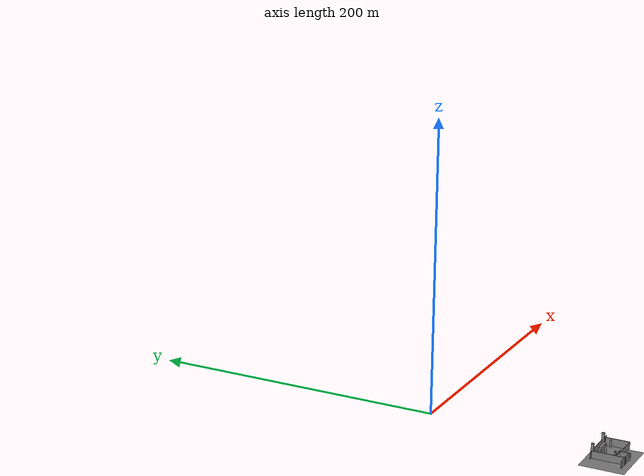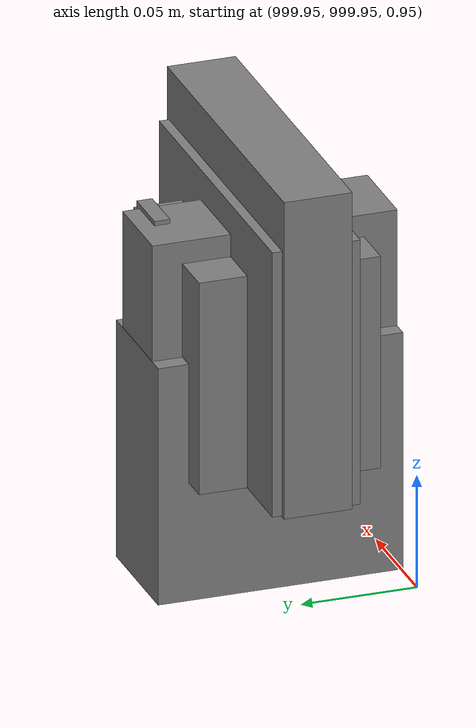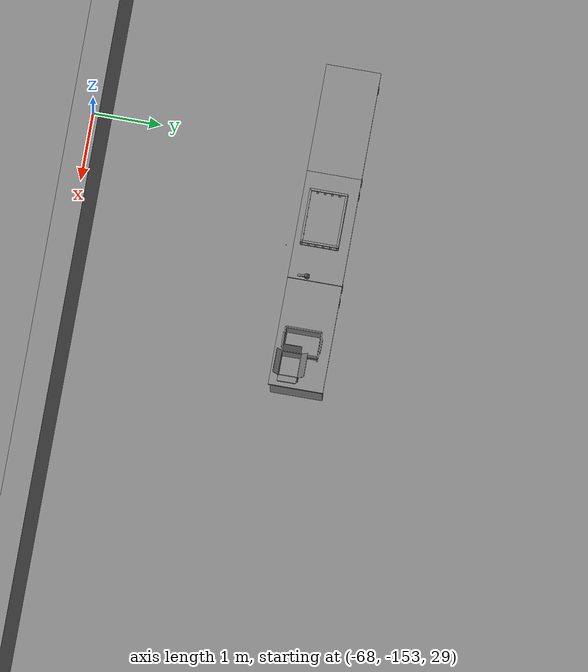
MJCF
<mujoco>
    <option gravity="0.000000000 0.000000000 -9.810000420" timestep="0.0049999999" integrator="implicitfast" density="1.225" viscosity="1.8000001e-05" noslip_iterations="10" iterations="100" sdf_iterations="50">
        <flag multiccd="disable"/>
    </option>
    <size memory="1000M"/>
    <compiler coordinate="local"/>
    <worldbody>
        <light cutoff="30" pos="0 1 1" dir="0 -1 -2"/>
        <light cutoff="30" pos="0 -1 1" dir="0 1 -2"/>
        <body pos="1000.000000000 1000.000000000 1.000000000" euler="0.000000000 0.000000000 180.000000000" name="openloong_gripper_2f85_fix_base_usda_battery_01">
            <geom contype="1" conaffinity="1" density="1000" type="box" material="" rgba="0.500000000 0.500000000 0.500000000 1.000000000" solimp="0.899999976 0.949999988 0.001000000" friction="1.000000000 0.005000000 0.000100000" solref="0.020000000 1.000000000" margin="0" condim="3" group="0" pos="-0.011123657 -0.041940309 0.101691343" quat="1.000000000 0.000000000 0.000000000 0.000000000" size="0.010800000 0.003375000 0.004725000" name="openloong_gripper_2f85_fix_base_usda_geom_28D83877_862F_48EB_B807_8627763D4573"/>
            <geom contype="1" conaffinity="1" density="1000" type="box" material="" rgba="0.500000000 0.500000000 0.500000000 1.000000000" solimp="0.899999976 0.949999988 0.001000000" friction="1.000000000 0.005000000 0.000100000" solref="0.020000000 1.000000000" margin="0" condim="3" group="0" pos="-0.010876465 -0.044247437 0.047066893" quat="0.998702705 -0.050920475 0.000000000 0.000000000" size="0.009450001 0.002700000 0.024975000" name="openloong_gripper_2f85_fix_base_usda_geom_85C3D115_959B_483D_8673_4FB2A7A020ED"/>
            <geom contype="1" conaffinity="1" density="1000" type="box" material="" rgba="0.500000000 0.500000000 0.500000000 1.000000000" solimp="0.899999976 0.949999988 0.001000000" friction="1.000000000 0.005000000 0.000100000" solref="0.020000000 1.000000000" margin="0" condim="3" group="0" pos="-0.001235962 -0.000659180 0.047381196" quat="1.000000000 0.000000000 0.000000000 0.000000000" size="0.039420001 0.039150000 0.047250003" name="openloong_gripper_2f85_fix_base_usda_geom_7DBD8C83_BC90_425C_8294_C4391D869FDD"/>
            <geom contype="1" conaffinity="1" density="1000" type="box" material="" rgba="0.500000000 0.500000000 0.500000000 1.000000000" solimp="0.899999976 0.949999988 0.001000000" friction="1.000000000 0.005000000 0.000100000" solref="0.020000000 1.000000000" margin="0" condim="3" group="0" pos="-0.010876465 -0.039138794 0.009851727" quat="1.000000000 0.000000000 0.000000000 0.000000000" size="0.009450001 0.010800000 0.013500000" name="openloong_gripper_2f85_fix_base_usda_geom_0C0C9792_3ABB_4F2C_98D8_32351FD0D2B7"/>
            <geom contype="1" conaffinity="1" density="1000" type="box" material="" rgba="0.500000000 0.500000000 0.500000000 1.000000000" solimp="0.899999976 0.949999988 0.001000000" friction="1.000000000 0.005000000 0.000100000" solref="0.020000000 1.000000000" margin="0" condim="3" group="0" pos="-0.010876465 -0.041528322 0.071508206" quat="1.000000000 0.000000000 0.000000000 0.000000000" size="0.009450001 0.002700000 0.027000001" name="openloong_gripper_2f85_fix_base_usda_geom_0468372E_5171_425A_A7A8_D8666E4A564E"/>
            <freejoint name="openloong_gripper_2f85_fix_base_usda_battery_01_joint"/>
            <site size="0.005000000 0.005000000 0.005000000" rgba="0.500000000 0.500000000 0.500000000 1.000000000" pos="0.000000000 0.000000000 0.000000000" quat="0.999961913 0.008726500 0.000000000 0.000000000" group="0" type="sphere" name="openloong_gripper_2f85_fix_base_usda_battery_01site"/>
        </body>
        <body pos="-65.836563110 -149.532852173 31.171171188" euler="94.113403320 -78.712928772 122.492141724" mocap="true" name="spotlight3_SpotLight"/>
        <body pos="1000.000000000 1000.000000000 1.000000000" euler="0.000000000 0.000000000 180.000000000" name="openloong_gripper_2f85_fix_base_usda_cpu_fan">
            <geom contype="1" conaffinity="1" density="1000" type="box" material="" rgba="0.500000000 0.500000000 0.500000000 1.000000000" solimp="0.899999976 0.949999988 0.001000000" friction="1.000000000 0.005000000 0.000100000" solref="0.020000000 1.000000000" margin="0" condim="3" group="0" pos="0.000000000 0.000000000 0.070034981" quat="0.000000000 0.000000000 0.000000000 1.000000000" size="0.070700005 0.014699999 0.070700005" name="openloong_gripper_2f85_fix_base_usda_geom_B1A6B71E_0812_4585_A27B_0CBCD3515205"/>
            <freejoint name="openloong_gripper_2f85_fix_base_usda_cpu_fan_joint"/>
            <site size="0.005000000 0.005000000 0.005000000" rgba="0.500000000 0.500000000 0.500000000 1.000000000" pos="0.000000000 0.000000000 0.000000000" quat="0.999961913 0.008726535 0.000000000 0.000000000" group="0" type="sphere" name="openloong_gripper_2f85_fix_base_usda_cpu_fancsite"/>
        </body>
        <body pos="1000.000000000 1000.000000000 1.000000000" euler="0.000000000 0.000000000 180.000000000" name="openloong_gripper_2f85_fix_base_usda_wifi_box">
            <geom contype="1" conaffinity="1" density="1000" type="box" material="" rgba="0.500000000 0.500000000 0.500000000 1.000000000" solimp="0.899999976 0.949999988 0.001000000" friction="1.000000000 0.005000000 0.000100000" solref="0.020000000 1.000000000" margin="0" condim="3" group="0" pos="0.000000000 0.000000000 0.058978677" quat="0.000000000 0.000000047 0.000000000 1.000000000" size="0.068499997 0.018999999 0.059000000" name="openloong_gripper_2f85_fix_base_usda_geom_A531A6AB_ED63_4607_A9B7_1CF8F47DE5BE"/>
            <freejoint name="openloong_gripper_2f85_fix_base_usda_wifi_box_joint"/>
            <site size="0.005000000 0.005000000 0.005000000" rgba="0.500000000 0.500000000 0.500000000 1.000000000" pos="0.000000000 0.000000000 0.000000000" quat="0.999961913 0.008726500 0.000000000 0.000000000" group="0" type="sphere" name="openloong_gripper_2f85_fix_base_usda_wifi_boxsite"/>
        </body>
        <body pos="-66.021812439 -149.541839600 31.162708282" euler="83.421905518 -83.213470459 118.465133667" mocap="true" name="spotlight6_SpotLight"/>
        <body pos="1000.000000000 1000.000000000 1.000000000" euler="0.000011953 0.000005123 -179.999984741" name="openloong_gripper_2f85_fix_base_usda_intel_box">
            <geom contype="1" conaffinity="1" density="1000" type="box" material="" rgba="0.500000000 0.500000000 0.500000000 1.000000000" solimp="0.899999976 0.949999988 0.001000000" friction="1.000000000 0.005000000 0.000100000" solref="0.020000000 1.000000000" margin="0" condim="3" group="0" pos="0.000000000 -0.000067139 0.000082284" quat="0.707106709 0.000000225 0.000000253 0.707106650" size="0.052800003 0.025300000 0.052800003" name="openloong_gripper_2f85_fix_base_usda_geom_D99440FA_099B_4EA6_B46F_E941B3AD3ADD"/>
            <freejoint name="openloong_gripper_2f85_fix_base_usda_intel_box_joint"/>
            <site size="0.005000000 0.005000000 0.005000000" rgba="0.500000000 0.500000000 0.500000000 1.000000000" pos="0.000000000 0.000000000 0.000000000" quat="0.999961913 0.008726500 0.000000000 0.000000000" group="0" type="sphere" name="openloong_gripper_2f85_fix_base_usda_intel_boxsite"/>
        </body>
        <body pos="1000.000000000 999.999938965 1.000000000" euler="0.000000000 0.000000000 180.000000000" name="openloong_gripper_2f85_fix_base_usda_intelcore_i5">
            <geom contype="1" conaffinity="1" density="1000" type="box" material="" rgba="0.500000000 0.500000000 0.500000000 1.000000000" solimp="0.899999976 0.949999988 0.001000000" friction="1.000000000 0.005000000 0.000100000" solref="0.020000000 1.000000000" margin="0" condim="3" group="0" pos="0.000000000 0.000000000 0.051722717" quat="0.707106709 0.000000000 0.000000000 -0.707106769" size="0.052800000 0.018080002 0.052800000" name="openloong_gripper_2f85_fix_base_usda_geom_7C18EEE7_719D_4F69_B344_E6B631AC6A00"/>
            <freejoint name="openloong_gripper_2f85_fix_base_usda_intelcore_i5_joint"/>
            <site size="0.005000000 0.005000000 0.005000000" rgba="0.500000000 0.500000000 0.500000000 1.000000000" pos="0.000000000 0.000000000 0.000000000" quat="0.999961913 0.008726534 0.000000000 0.000000000" group="0" type="sphere" name="openloong_gripper_2f85_fix_base_usda_intelcore_i5site"/>
        </body>
        <body pos="-66.129928589 -149.230346680 31.168804169" euler="151.557296753 -18.737884521 -60.313819885" mocap="true" name="spotlight1_SpotLight"/>
        <body pos="-64.866622925 -149.383972168 30.183746338" euler="89.999984741 89.999946594 0.000000000" name="openloong_gripper_2f85_fix_base_usda_bluebox_01">
            <geom contype="1" conaffinity="1" density="1000" type="box" material="" rgba="0.500000000 0.500000000 0.500000000 1.000000000" solimp="0.899999976 0.949999988 0.001000000" friction="1.000000000 0.005000000 0.000100000" solref="0.020000000 1.000000000" margin="0" condim="3" group="0" pos="0.276580811 0.187225342 0.000068665" quat="0.707106948 0.000077471 0.707106352 0.000077486" size="0.100000001 0.057999998 0.010000000" name="openloong_gripper_2f85_fix_base_usda_geom_B8C8690C_2DF3_4601_9D1C_96EC046CF6BA"/>
            <geom contype="1" conaffinity="1" density="1000" type="box" material="" rgba="0.500000000 0.500000000 0.500000000 1.000000000" solimp="0.899999976 0.949999988 0.001000000" friction="1.000000000 0.005000000 0.000100000" solref="0.020000000 1.000000000" margin="0" condim="3" group="0" pos="0.000000000 0.002883911 0.000000000" quat="0.999999881 0.000000000 0.000000000 0.000000000" size="0.254000008 0.003000000 0.172000006" name="openloong_gripper_2f85_fix_base_usda_geom_E3870211_EA36_4067_BEE6_8506B475B12A"/>
            <geom contype="1" conaffinity="1" density="1000" type="box" material="" rgba="0.500000000 0.500000000 0.500000000 1.000000000" solimp="0.899999976 0.949999988 0.001000000" friction="1.000000000 0.005000000 0.000100000" solref="0.020000000 1.000000000" margin="0" condim="3" group="0" pos="0.000000000 0.124874115 0.173484802" quat="0.999796331 0.020176515 -0.000000015 0.000000030" size="0.259999990 0.119999997 0.007000000" name="openloong_gripper_2f85_fix_base_usda_geom_78B57FF7_FC0F_45FC_A5A3_446F455D31A3"/>
            <geom contype="1" conaffinity="1" density="1000" type="box" material="" rgba="0.500000000 0.500000000 0.500000000 1.000000000" solimp="0.899999976 0.949999988 0.001000000" friction="1.000000000 0.005000000 0.000100000" solref="0.020000000 1.000000000" margin="0" condim="3" group="0" pos="0.000000000 0.124874115 -0.173469543" quat="0.999796331 -0.020176545 -0.000000015 0.000000000" size="0.259999990 0.119999997 0.007000000" name="openloong_gripper_2f85_fix_base_usda_geom_03744FBF_8A8B_4073_BCD7_CA9365E3B78B"/>
            <geom contype="1" conaffinity="1" density="1000" type="box" material="" rgba="0.500000000 0.500000000 0.500000000 1.000000000" solimp="0.899999976 0.949999988 0.001000000" friction="1.000000000 0.005000000 0.000100000" solref="0.020000000 1.000000000" margin="0" condim="3" group="0" pos="0.000000000 0.214008331 0.188980103" quat="0.999912977 0.013176724 0.000000015 0.000000000" size="0.259999990 0.029999999 0.012500000" name="openloong_gripper_2f85_fix_base_usda_geom_64A11B42_CF1D_48F3_9019_E00C8E090625"/>
            <geom contype="1" conaffinity="1" density="1000" type="box" material="" rgba="0.500000000 0.500000000 0.500000000 1.000000000" solimp="0.899999976 0.949999988 0.001000000" friction="1.000000000 0.005000000 0.000100000" solref="0.020000000 1.000000000" margin="0" condim="3" group="0" pos="-0.258361816 0.125289917 0.001876831" quat="0.702796936 -0.020792112 0.710783124 0.020769298" size="0.189999998 0.119999997 0.009000000" name="openloong_gripper_2f85_fix_base_usda_geom_5012A555_89D0_4EEB_AE8E_2D1369808C48"/>
            <geom contype="1" conaffinity="1" density="1000" type="box" material="" rgba="0.500000000 0.500000000 0.500000000 1.000000000" solimp="0.899999976 0.949999988 0.001000000" friction="1.000000000 0.005000000 0.000100000" solref="0.020000000 1.000000000" margin="0" condim="3" group="0" pos="0.000000000 0.214008331 -0.188980103" quat="0.999912977 -0.013176769 0.000000030 0.000000015" size="0.259999990 0.029999999 0.012500000" name="openloong_gripper_2f85_fix_base_usda_geom_58C1ADC3_0C24_4BE5_BEDD_F4B8F66A9EB5"/>
            <geom contype="1" conaffinity="1" density="1000" type="box" material="" rgba="0.500000000 0.500000000 0.500000000 1.000000000" solimp="0.899999976 0.949999988 0.001000000" friction="1.000000000 0.005000000 0.000100000" solref="0.020000000 1.000000000" margin="0" condim="3" group="0" pos="-0.276611328 0.187225342 0.000068665" quat="0.707106650 0.000077441 0.707106709 0.000077456" size="0.100000001 0.057999998 0.010000000" name="openloong_gripper_2f85_fix_base_usda_geom_AF9689A3_2D94_41C6_8197_89AF80C7D648"/>
            <geom contype="1" conaffinity="1" density="1000" type="box" material="" rgba="0.500000000 0.500000000 0.500000000 1.000000000" solimp="0.899999976 0.949999988 0.001000000" friction="1.000000000 0.005000000 0.000100000" solref="0.020000000 1.000000000" margin="0" condim="3" group="0" pos="0.258331299 0.125289917 0.001876831" quat="0.702851415 0.018856421 0.710823774 -0.019329369" size="0.189999998 0.119999997 0.009000000" name="openloong_gripper_2f85_fix_base_usda_geom_9F0D4E4B_792F_43BA_8642_A556F823A6FB"/>
            <freejoint name="openloong_gripper_2f85_fix_base_usda_bluebox_01_joint"/>
            <site size="0.005000000 0.005000000 0.005000000" rgba="0.500000000 0.500000000 0.500000000 1.000000000" pos="0.000000000 0.000000000 0.000000000" quat="0.999961913 0.008726534 0.000000000 0.000000000" group="0" type="sphere" name="openloong_gripper_2f85_fix_base_usda_bluebox_01site"/>
        </body>
        <body pos="-64.496299744 -149.491867065 30.235729218" euler="0.000000000 0.000000000 89.999946594" name="openloong_gripper_2f85_fix_base_usda_cardboardbox_01">
            <geom contype="1" conaffinity="1" density="1000" type="box" material="" rgba="0.500000000 0.500000000 0.500000000 1.000000000" solimp="0.899999976 0.949999988 0.001000000" friction="1.000000000 0.005000000 0.000100000" solref="0.020000000 1.000000000" margin="0" condim="3" group="0" pos="-0.003166199 -0.004086494 0.005052090" quat="1.000000000 0.000000000 0.000000000 0.000000000" size="0.142499998 0.177500010 0.005000000" name="openloong_gripper_2f85_fix_base_usda_geom_A8CF156C_4199_4838_B9C4_FAE44338B05A"/>
            <geom contype="1" conaffinity="1" density="1000" type="box" material="" rgba="0.500000000 0.500000000 0.500000000 1.000000000" solimp="0.899999976 0.949999988 0.001000000" friction="1.000000000 0.005000000 0.000100000" solref="0.020000000 1.000000000" margin="0" condim="3" group="0" pos="-0.003166199 0.170316696 0.150570869" quat="1.000000000 0.000000000 0.000000000 0.000000000" size="0.142499998 0.005000000 0.149999991" name="openloong_gripper_2f85_fix_base_usda_geom_4DDFB20B_771C_43E3_93F2_081197483F03"/>
            <geom contype="1" conaffinity="1" density="1000" type="box" material="" rgba="0.500000000 0.500000000 0.500000000 1.000000000" solimp="0.899999976 0.949999988 0.001000000" friction="1.000000000 0.005000000 0.000100000" solref="0.020000000 1.000000000" margin="0" condim="3" group="0" pos="-0.147399902 -0.005307198 0.150570869" quat="1.000000000 0.000000000 0.000000000 0.000000000" size="0.005000000 0.177500010 0.149999991" name="openloong_gripper_2f85_fix_base_usda_geom_72BA2985_10DB_4E3D_B806_751F36EC8AC1"/>
            <geom contype="1" conaffinity="1" density="1000" type="box" material="" rgba="0.500000000 0.500000000 0.500000000 1.000000000" solimp="0.899999976 0.949999988 0.001000000" friction="1.000000000 0.005000000 0.000100000" solref="0.020000000 1.000000000" margin="0" condim="3" group="0" pos="0.140275955 -0.005307198 0.150570869" quat="1.000000000 0.000000000 0.000000000 0.000000000" size="0.005000000 0.177500010 0.149999991" name="openloong_gripper_2f85_fix_base_usda_geom_8AEFB86A_0278_4034_96B2_05139801E184"/>
            <geom contype="1" conaffinity="1" density="1000" type="box" material="" rgba="0.500000000 0.500000000 0.500000000 1.000000000" solimp="0.899999976 0.949999988 0.001000000" friction="1.000000000 0.005000000 0.000100000" solref="0.020000000 1.000000000" margin="0" condim="3" group="0" pos="-0.003166199 -0.181550980 0.150570869" quat="1.000000000 0.000000000 0.000000000 0.000000000" size="0.142499998 0.005000000 0.149999991" name="openloong_gripper_2f85_fix_base_usda_geom_7E394E4D_6652_413D_9ECC_995A936B558C"/>
            <freejoint name="openloong_gripper_2f85_fix_base_usda_cardboardbox_01_joint"/>
            <site size="0.005000000 0.005000000 0.005000000" rgba="0.500000000 0.500000000 0.500000000 1.000000000" pos="0.000000000 0.000000000 0.000000000" quat="0.999961913 0.008726535 0.000000000 0.000000000" group="0" type="sphere" name="openloong_gripper_2f85_fix_base_usda_site_3A53C1B6_F9B5_4D02_9594_52349C57DB68"/>
            <body pos="0.139160156 -0.004048347 0.301930904" euler="-179.999954224 49.383502960 179.999954224" name="openloong_gripper_2f85_fix_base_usda_A1_006">
                <geom contype="1" conaffinity="1" density="1000" type="box" material="" rgba="0.500000000 0.500000000 0.500000000 1.000000000" solimp="0.899999976 0.949999988 0.001000000" friction="1.000000000 0.005000000 0.000100000" solref="0.020000000 1.000000000" margin="0" condim="3" group="0" pos="-0.071587563 0.000009537 0.001745224" quat="0.999999881 0.000000000 0.000000000 0.000000000" size="0.071249999 0.179999992 0.002500000" name="openloong_gripper_2f85_fix_base_usda_geom_250D0B6A_FC1E_46B6_B1F4_38ABEB05C092"/>
                <joint armature="0" stiffness="0.07" damping="0.0099999998" axis="0.000000 1.000000 0.000000" type="hinge" name="openloong_gripper_2f85_fix_base_usda_A1_006"/>
            </body>
            <body pos="-0.145902634 -0.004086494 0.301938057" euler="-180.000000000 -60.000011444 -180.000000000" name="openloong_gripper_2f85_fix_base_usda_A2_006">
                <geom contype="1" conaffinity="1" density="1000" type="box" material="" rgba="0.500000000 0.500000000 0.500000000 1.000000000" solimp="0.899999976 0.949999988 0.001000000" friction="1.000000000 0.005000000 0.000100000" solref="0.020000000 1.000000000" margin="0" condim="3" group="0" pos="0.071268082 0.000009537 0.002717972" quat="0.000002921 0.000000000 -0.000000030 0.999999881" size="0.071249999 0.179999992 0.002500000" name="openloong_gripper_2f85_fix_base_usda_geom_1617C217_AF59_4508_9D88_EBE332185F08"/>
                <joint armature="0" stiffness="0.07" damping="0.0099999998" axis="0.000000 1.000000 0.000000" type="hinge" name="openloong_gripper_2f85_fix_base_usda_A2_006"/>
            </body>
            <body pos="-0.003385544 0.175991058 0.301930904" euler="-125.858116150 -0.000004561 0.000002331" name="openloong_gripper_2f85_fix_base_usda_B2_006">
                <geom contype="1" conaffinity="1" density="1000" type="box" material="" rgba="0.500000000 0.500000000 0.500000000 1.000000000" solimp="0.899999976 0.949999988 0.001000000" friction="1.000000000 0.005000000 0.000100000" solref="0.020000000 1.000000000" margin="0" condim="3" group="0" pos="0.000009537 -0.070939064 -0.002470016" quat="0.999614120 0.027776197 -0.000000015 0.000000030" size="0.137500003 0.064999998 0.005000000" name="openloong_gripper_2f85_fix_base_usda_geom_332075E2_3324_4FE7_A690_FAF2F7679AB9"/>
                <joint armature="0" stiffness="0.07" damping="0.0099999998" axis="1.000000 0.000000 0.000000" type="hinge" name="openloong_gripper_2f85_fix_base_usda_B2_006"/>
            </body>
            <body pos="-0.003385544 -0.184140205 0.301938057" euler="147.805557251 0.000000000 0.000000000" name="openloong_gripper_2f85_fix_base_usda_B1_006">
                <geom contype="1" conaffinity="1" density="1000" type="box" material="" rgba="0.500000000 0.500000000 0.500000000 1.000000000" solimp="0.899999976 0.949999988 0.001000000" friction="1.000000000 0.005000000 0.000100000" solref="0.020000000 1.000000000" margin="0" condim="3" group="0" pos="-0.000028610 0.070202351 -0.002703667" quat="0.999614179 -0.027776167 0.000000000 0.000000000" size="0.137500003 0.064999998 0.005000000" name="openloong_gripper_2f85_fix_base_usda_geom_8AF6DD8A_D4C9_4F7C_BE66_D4932B51E421"/>
                <joint armature="0" stiffness="0.07" damping="0.0099999998" axis="1.000000 0.000000 0.000000" type="hinge" name="openloong_gripper_2f85_fix_base_usda_B1_006"/>
            </body>
        </body>
        <body pos="-65.882858276 -149.481979370 30.229999542" euler="-64.487716675 0.000000000 0.000000000" name="openloong_gripper_2f85_fix_base_usda_Barcode">
            <geom contype="1" conaffinity="1" density="1000" type="box" material="" rgba="0.500000000 0.500000000 0.500000000 1.000000000" solimp="0.899999976 0.949999988 0.001000000" friction="1.000000000 0.005000000 0.000100000" solref="0.020000000 1.000000000" margin="0" condim="3" group="0" pos="0.000000000 0.013038635 0.001419067" quat="0.000000000 0.000000000 0.000000000 1.000000119" size="0.034000002 0.010000000 0.017999999" name="openloong_gripper_2f85_fix_base_usda_geom_3FCA3BDC_EE55_46CE_8B87_51B98163CA20"/>
            <geom contype="1" conaffinity="1" density="1000" type="box" material="" rgba="0.500000000 0.500000000 0.500000000 1.000000000" solimp="0.899999976 0.949999988 0.001000000" friction="1.000000000 0.005000000 0.000100000" solref="0.020000000 1.000000000" margin="0" condim="3" group="0" pos="0.000000000 -0.035301208 -0.007095337" quat="0.000000000 0.000000000 -0.043619365 0.999048233" size="0.028999999 0.010000000 0.020000000" name="openloong_gripper_2f85_fix_base_usda_geom_7AB3D8B7_6144_41A6_806A_07E7DF285C25"/>
            <geom contype="1" conaffinity="1" density="1000" type="box" material="" rgba="0.500000000 0.500000000 0.500000000 1.000000000" solimp="0.899999976 0.949999988 0.001000000" friction="1.000000000 0.005000000 0.000100000" solref="0.020000000 1.000000000" margin="0" condim="3" group="0" pos="0.000000000 -0.043411255 -0.011749268" quat="0.922262907 0.386563420 0.000000000 0.000000000" size="0.026000001 0.010000000 0.020000000" name="openloong_gripper_2f85_fix_base_usda_geom_5E88611C_6FBC_45E1_B0E1_EC0BB90E4F82"/>
            <geom contype="1" conaffinity="1" density="1000" type="box" material="" rgba="0.500000000 0.500000000 0.500000000 1.000000000" solimp="0.899999976 0.949999988 0.001000000" friction="1.000000000 0.005000000 0.000100000" solref="0.020000000 1.000000000" margin="0" condim="3" group="0" pos="0.000000000 -0.016967773 -0.031860352" quat="0.000000000 0.000000000 0.000000000 1.000000119" size="0.008000000 0.010000000 0.013000000" name="openloong_gripper_2f85_fix_base_usda_geom_1D70BDBF_3DC0_4BB3_AF1C_B8660C8353A8"/>
            <geom contype="1" conaffinity="1" density="1000" type="box" material="" rgba="0.500000000 0.500000000 0.500000000 1.000000000" solimp="0.899999976 0.949999988 0.001000000" friction="1.000000000 0.005000000 0.000100000" solref="0.020000000 1.000000000" margin="0" condim="3" group="0" pos="0.000000000 -0.001869202 0.000312805" quat="0.953716993 0.300705761 0.000000000 0.000000000" size="0.032000002 0.010000000 0.018999999" name="openloong_gripper_2f85_fix_base_usda_geom_619F1576_E2D7_4904_AB06_0B2B98821DC1"/>
            <geom contype="1" conaffinity="1" density="1000" type="box" material="" rgba="0.500000000 0.500000000 0.500000000 1.000000000" solimp="0.899999976 0.949999988 0.001000000" friction="1.000000000 0.005000000 0.000100000" solref="0.020000000 1.000000000" margin="0" condim="3" group="0" pos="0.000000000 -0.019531250 -0.003173828" quat="0.953716993 0.300705761 0.000000000 0.000000000" size="0.030999999 0.010000000 0.020000000" name="openloong_gripper_2f85_fix_base_usda_geom_3709EF13_6EBA_4EF1_908C_CF849E0D144D"/>
            <geom contype="1" conaffinity="1" density="1000" type="box" material="" rgba="0.500000000 0.500000000 0.500000000 1.000000000" solimp="0.899999976 0.949999988 0.001000000" friction="1.000000000 0.005000000 0.000100000" solref="0.020000000 1.000000000" margin="0" condim="3" group="0" pos="0.000000000 -0.035301208 -0.007095337" quat="0.953716993 0.300705761 0.000000000 0.000000000" size="0.028999999 0.010000000 0.020000000" name="openloong_gripper_2f85_fix_base_usda_geom_AB6CE227_0A71_43F6_BDB6_9B2785FB3ABE"/>
            <geom contype="1" conaffinity="1" density="1000" type="box" material="" rgba="0.500000000 0.500000000 0.500000000 1.000000000" solimp="0.899999976 0.949999988 0.001000000" friction="1.000000000 0.005000000 0.000100000" solref="0.020000000 1.000000000" margin="0" condim="3" group="0" pos="0.000000000 -0.042617798 -0.071121216" quat="0.000000000 0.000000000 0.000000000 1.000000119" size="0.013000000 0.021000000 0.059999999" name="openloong_gripper_2f85_fix_base_usda_geom_6475E2D4_8568_440D_8108_A24648C80B5E"/>
            <freejoint name="openloong_gripper_2f85_fix_base_usda_Barcode_joint"/>
            <site size="0.005000000 0.005000000 0.005000000" rgba="0.500000000 0.500000000 0.500000000 1.000000000" pos="0.000000000 0.000000000 0.000000000" quat="1.000000000 0.000000000 0.000000000 0.000000000" group="0" type="sphere" name="openloong_gripper_2f85_fix_base_usda_Barcode_site"/>
        </body>
        <body pos="-66.745018005 -149.392349243 30.184000015" euler="0.000000000 0.000000000 89.999946594" name="[22329940005937]_Basket_01">
            <geom contype="1" conaffinity="1" density="1000" type="box" material="" rgba="0.500000000 0.500000000 0.500000000 1.000000000" solimp="0.899999976 0.949999988 0.001000000" friction="1.000000000 0.005000000 0.000100000" solref="0.020000000 1.000000000" margin="0" condim="3" group="0" pos="-0.052425385 0.389207840 0.089787483" quat="0.707107008 0.000000000 0.000000000 0.707106411" size="0.014249999 0.014249999 0.059999999" name="[22329940005937]_geom_0090342D_C297_41B5_8A1B_BDDE783EBBCC"/>
            <geom contype="1" conaffinity="1" density="1000" type="box" material="" rgba="0.500000000 0.500000000 0.500000000 1.000000000" solimp="0.899999976 0.949999988 0.001000000" friction="1.000000000 0.005000000 0.000100000" solref="0.020000000 1.000000000" margin="0" condim="3" group="0" pos="0.264015198 -0.133043289 0.089787483" quat="0.707107008 0.000000000 0.000000000 0.707106411" size="0.014249999 0.014249999 0.059999999" name="[22329940005937]_geom_B1315F79_0A0A_40D6_9FCC_C832D97719E6"/>
            <geom contype="1" conaffinity="1" density="1000" type="box" material="" rgba="0.500000000 0.500000000 0.500000000 1.000000000" solimp="0.899999976 0.949999988 0.001000000" friction="1.000000000 0.005000000 0.000100000" solref="0.020000000 1.000000000" margin="0" condim="3" group="0" pos="-0.264015198 -0.265548706 0.089793205" quat="0.707107008 0.000000000 0.000000000 0.707106411" size="0.014249999 0.014249999 0.059999999" name="[22329940005937]_geom_5DA2396C_5150_4E33_8078_30F8B3598879"/>
            <geom contype="1" conaffinity="1" density="1000" type="box" material="" rgba="0.500000000 0.500000000 0.500000000 1.000000000" solimp="0.899999976 0.949999988 0.001000000" friction="1.000000000 0.005000000 0.000100000" solref="0.020000000 1.000000000" margin="0" condim="3" group="0" pos="-0.160263062 -0.389322281 0.089793205" quat="0.707107008 0.000000000 0.000000000 0.707106411" size="0.014249999 0.014249999 0.059999999" name="[22329940005937]_geom_7896F1D5_34A8_4941_AE62_844AD0AEB5AE"/>
            <geom contype="1" conaffinity="1" density="1000" type="box" material="" rgba="0.500000000 0.500000000 0.500000000 1.000000000" solimp="0.899999976 0.949999988 0.001000000" friction="1.000000000 0.005000000 0.000100000" solref="0.020000000 1.000000000" margin="0" condim="3" group="0" pos="0.162265778 -0.389322281 0.089787483" quat="0.707107008 0.000000000 0.000000000 0.707106411" size="0.014249999 0.014249999 0.059999999" name="[22329940005937]_geom_9A26BD34_4E76_4F70_9845_7BA22FB33BCF"/>
            <geom contype="1" conaffinity="1" density="1000" type="box" material="" rgba="0.500000000 0.500000000 0.500000000 1.000000000" solimp="0.899999976 0.949999988 0.001000000" friction="1.000000000 0.005000000 0.000100000" solref="0.020000000 1.000000000" margin="0" condim="3" group="0" pos="0.264015198 0.389207840 0.089787483" quat="0.707107008 0.000000000 0.000000000 0.707106411" size="0.014249999 0.014249999 0.059999999" name="[22329940005937]_geom_182B9A43_567F_44EC_96A5_A4108BF6A6D0"/>
            <geom contype="1" conaffinity="1" density="1000" type="box" material="" rgba="0.500000000 0.500000000 0.500000000 1.000000000" solimp="0.899999976 0.949999988 0.001000000" friction="1.000000000 0.005000000 0.000100000" solref="0.020000000 1.000000000" margin="0" condim="3" group="0" pos="-0.264015198 -0.133043289 0.089793205" quat="0.707107008 0.000000000 0.000000000 0.707106411" size="0.014249999 0.014249999 0.059999999" name="[22329940005937]_geom_E6428F1D_CE09_42AE_B3F8_87E46140E77F"/>
            <geom contype="1" conaffinity="1" density="1000" type="box" material="" rgba="0.500000000 0.500000000 0.500000000 1.000000000" solimp="0.899999976 0.949999988 0.001000000" friction="1.000000000 0.005000000 0.000100000" solref="0.020000000 1.000000000" margin="0" condim="3" group="0" pos="-0.264026642 0.269256592 0.089793205" quat="0.707107008 0.000000000 0.000000000 0.707106411" size="0.014249999 0.014249999 0.059999999" name="[22329940005937]_geom_388C9755_1E49_4C28_900C_990C0746C81A"/>
            <geom contype="1" conaffinity="1" density="1000" type="box" material="" rgba="0.500000000 0.500000000 0.500000000 1.000000000" solimp="0.899999976 0.949999988 0.001000000" friction="1.000000000 0.005000000 0.000100000" solref="0.020000000 1.000000000" margin="0" condim="3" group="0" pos="0.054462433 0.389207840 0.089787483" quat="0.707107008 0.000000000 0.000000000 0.707106411" size="0.014249999 0.014249999 0.059999999" name="[22329940005937]_geom_645DDF6C_46E3_47BF_894C_A39DDC939A9C"/>
            <geom contype="1" conaffinity="1" density="1000" type="box" material="" rgba="0.500000000 0.500000000 0.500000000 1.000000000" solimp="0.899999976 0.949999988 0.001000000" friction="1.000000000 0.005000000 0.000100000" solref="0.020000000 1.000000000" margin="0" condim="3" group="0" pos="0.054462433 -0.389322281 0.089787483" quat="0.707107008 0.000000000 0.000000000 0.707106411" size="0.014249999 0.014249999 0.059999999" name="[22329940005937]_geom_20682785_DC05_45F7_9019_D684E2717C98"/>
            <geom contype="1" conaffinity="1" density="1000" type="box" material="" rgba="0.500000000 0.500000000 0.500000000 1.000000000" solimp="0.899999976 0.949999988 0.001000000" friction="1.000000000 0.005000000 0.000100000" solref="0.020000000 1.000000000" margin="0" condim="3" group="0" pos="0.264015198 0.269256592 0.089793205" quat="0.707107008 0.000000000 0.000000000 0.707106411" size="0.014249999 0.014249999 0.059999999" name="[22329940005937]_geom_01B3BC44_9812_44F2_AB8B_E98A53A46106"/>
            <geom contype="1" conaffinity="1" density="1000" type="box" material="" rgba="0.500000000 0.500000000 0.500000000 1.000000000" solimp="0.899999976 0.949999988 0.001000000" friction="1.000000000 0.005000000 0.000100000" solref="0.020000000 1.000000000" margin="0" condim="3" group="0" pos="0.264015198 -0.389322281 0.089787483" quat="0.707107008 0.000000000 0.000000000 0.707106411" size="0.014249999 0.014249999 0.059999999" name="[22329940005937]_geom_4C659822_53B2_47A8_B628_5EC3A42C8DC0"/>
            <geom contype="1" conaffinity="1" density="1000" type="box" material="" rgba="0.500000000 0.500000000 0.500000000 1.000000000" solimp="0.899999976 0.949999988 0.001000000" friction="1.000000000 0.005000000 0.000100000" solref="0.020000000 1.000000000" margin="0" condim="3" group="0" pos="0.000000000 0.000000000 0.015998840" quat="0.707107008 0.000000000 0.000000000 0.707106411" size="0.403499991 0.279000014 0.015750000" name="[22329940005937]_geom_AEC74B1D_081D_45FB_97A4_0697711F1578"/>
            <geom contype="1" conaffinity="1" density="1000" type="box" material="" rgba="0.500000000 0.500000000 0.500000000 1.000000000" solimp="0.899999976 0.949999988 0.001000000" friction="1.000000000 0.005000000 0.000100000" solref="0.020000000 1.000000000" margin="0" condim="3" group="0" pos="0.000000000 -0.389476776 0.163619041" quat="0.707107008 0.000000000 0.000000000 0.707106411" size="0.015000000 0.277500004 0.015750000" name="[22329940005937]_geom_DFA85023_2C36_4808_BE3A_635AC3A9EEA3"/>
            <geom contype="1" conaffinity="1" density="1000" type="box" material="" rgba="0.500000000 0.500000000 0.500000000 1.000000000" solimp="0.899999976 0.949999988 0.001000000" friction="1.000000000 0.005000000 0.000100000" solref="0.020000000 1.000000000" margin="0" condim="3" group="0" pos="0.162265778 0.389207840 0.089787483" quat="0.707107008 0.000000000 0.000000000 0.707106411" size="0.014249999 0.014249999 0.059999999" name="[22329940005937]_geom_A5877914_A4CC_41BA_841E_4FF4122855B6"/>
            <geom contype="1" conaffinity="1" density="1000" type="box" material="" rgba="0.500000000 0.500000000 0.500000000 1.000000000" solimp="0.899999976 0.949999988 0.001000000" friction="1.000000000 0.005000000 0.000100000" solref="0.020000000 1.000000000" margin="0" condim="3" group="0" pos="0.000000000 0.389471054 0.163619041" quat="0.707107008 0.000000000 0.000000000 0.707106411" size="0.015000000 0.277500004 0.015750000" name="[22329940005937]_geom_47C2E0BD_100A_402D_A3F4_5AB4F8D0051C"/>
            <geom contype="1" conaffinity="1" density="1000" type="box" material="" rgba="0.500000000 0.500000000 0.500000000 1.000000000" solimp="0.899999976 0.949999988 0.001000000" friction="1.000000000 0.005000000 0.000100000" solref="0.020000000 1.000000000" margin="0" condim="3" group="0" pos="-0.263511658 0.000000000 0.163619041" quat="0.707107008 0.000000000 0.000000000 0.707106411" size="0.403499991 0.015000000 0.015750000" name="[22329940005937]_geom_E6132EA4_491C_46D8_BD95_B5990AC3804B"/>
            <geom contype="1" conaffinity="1" density="1000" type="box" material="" rgba="0.500000000 0.500000000 0.500000000 1.000000000" solimp="0.899999976 0.949999988 0.001000000" friction="1.000000000 0.005000000 0.000100000" solref="0.020000000 1.000000000" margin="0" condim="3" group="0" pos="-0.264015198 0.141334534 0.089793205" quat="0.707107008 0.000000000 0.000000000 0.707106411" size="0.014249999 0.014249999 0.059999999" name="[22329940005937]_geom_B3DD5742_65C0_4C64_997D_A3FA1E63819D"/>
            <geom contype="1" conaffinity="1" density="1000" type="box" material="" rgba="0.500000000 0.500000000 0.500000000 1.000000000" solimp="0.899999976 0.949999988 0.001000000" friction="1.000000000 0.005000000 0.000100000" solref="0.020000000 1.000000000" margin="0" condim="3" group="0" pos="0.264015198 -0.265548706 0.089787483" quat="0.707107008 0.000000000 0.000000000 0.707106411" size="0.014249999 0.014249999 0.059999999" name="[22329940005937]_geom_33093ADD_D14A_4614_9665_BF1D82C6FBBA"/>
            <geom contype="1" conaffinity="1" density="1000" type="box" material="" rgba="0.500000000 0.500000000 0.500000000 1.000000000" solimp="0.899999976 0.949999988 0.001000000" friction="1.000000000 0.005000000 0.000100000" solref="0.020000000 1.000000000" margin="0" condim="3" group="0" pos="-0.160263062 0.389207840 0.089787483" quat="0.707107008 0.000000000 0.000000000 0.707106411" size="0.014249999 0.014249999 0.059999999" name="[22329940005937]_geom_10D4C53E_5F6A_4859_A67A_21DB8B601C23"/>
            <geom contype="1" conaffinity="1" density="1000" type="box" material="" rgba="0.500000000 0.500000000 0.500000000 1.000000000" solimp="0.899999976 0.949999988 0.001000000" friction="1.000000000 0.005000000 0.000100000" solref="0.020000000 1.000000000" margin="0" condim="3" group="0" pos="-0.052425385 -0.389322281 0.089787483" quat="0.707107008 0.000000000 0.000000000 0.707106411" size="0.014249999 0.014249999 0.059999999" name="[22329940005937]_geom_BE0903F8_2B12_4C92_B1F6_0434DA77D370"/>
            <geom contype="1" conaffinity="1" density="1000" type="box" material="" rgba="0.500000000 0.500000000 0.500000000 1.000000000" solimp="0.899999976 0.949999988 0.001000000" friction="1.000000000 0.005000000 0.000100000" solref="0.020000000 1.000000000" margin="0" condim="3" group="0" pos="-0.264026642 -0.389322281 0.089793205" quat="0.707107008 0.000000000 0.000000000 0.707106411" size="0.014249999 0.014249999 0.059999999" name="[22329940005937]_geom_38271DCC_E47C_4C5F_B8A9_B66D0E0E5289"/>
            <geom contype="1" conaffinity="1" density="1000" type="box" material="" rgba="0.500000000 0.500000000 0.500000000 1.000000000" solimp="0.899999976 0.949999988 0.001000000" friction="1.000000000 0.005000000 0.000100000" solref="0.020000000 1.000000000" margin="0" condim="3" group="0" pos="0.264015198 0.141334534 0.089787483" quat="0.707107008 0.000000000 0.000000000 0.707106411" size="0.014249999 0.014249999 0.059999999" name="[22329940005937]_geom_8AE23F87_2C84_4C7E_A4D9_ED21AD9321F6"/>
            <geom contype="1" conaffinity="1" density="1000" type="box" material="" rgba="0.500000000 0.500000000 0.500000000 1.000000000" solimp="0.899999976 0.949999988 0.001000000" friction="1.000000000 0.005000000 0.000100000" solref="0.020000000 1.000000000" margin="0" condim="3" group="0" pos="-0.264015198 0.389207840 0.089793205" quat="0.707107008 0.000000000 0.000000000 0.707106411" size="0.014249999 0.014249999 0.059999999" name="[22329940005937]_geom_51DFB1FE_4DDE_4B2D_8278_F756624662C6"/>
            <geom contype="1" conaffinity="1" density="1000" type="box" material="" rgba="0.500000000 0.500000000 0.500000000 1.000000000" solimp="0.899999976 0.949999988 0.001000000" friction="1.000000000 0.005000000 0.000100000" solref="0.020000000 1.000000000" margin="0" condim="3" group="0" pos="0.264015198 0.004480362 0.089787483" quat="0.707107008 0.000000000 0.000000000 0.707106411" size="0.014249999 0.014249999 0.059999999" name="[22329940005937]_geom_1B8F28D2_FB36_4DEE_9970_B9F897C19540"/>
            <geom contype="1" conaffinity="1" density="1000" type="box" material="" rgba="0.500000000 0.500000000 0.500000000 1.000000000" solimp="0.899999976 0.949999988 0.001000000" friction="1.000000000 0.005000000 0.000100000" solref="0.020000000 1.000000000" margin="0" condim="3" group="0" pos="0.263694763 -0.000011444 0.163619041" quat="0.707107008 0.000000000 0.000000000 0.707106411" size="0.403499991 0.015000000 0.015750000" name="[22329940005937]_geom_6BF92E09_290D_4BC7_8231_BA6DC026A788"/>
            <geom contype="1" conaffinity="1" density="1000" type="box" material="" rgba="0.500000000 0.500000000 0.500000000 1.000000000" solimp="0.899999976 0.949999988 0.001000000" friction="1.000000000 0.005000000 0.000100000" solref="0.020000000 1.000000000" margin="0" condim="3" group="0" pos="-0.264015198 0.004480362 0.089793205" quat="0.707107008 0.000000000 0.000000000 0.707106411" size="0.014249999 0.014249999 0.059999999" name="[22329940005937]_geom_CC97DF1C_B98E_458F_A050_B71C47EB09AA"/>
            <freejoint name="[22329940005937]_joint_A8777AE6_63B1_4BD3_B119_3C0CEF0E0551"/>
        </body>
        <body pos="0.000000000 0.000000000 0.000000000" euler="0.000000000 0.000000000 0.000000000" name="Static Objects_Static Objects">
            <geom contype="1" conaffinity="1" density="1000" type="box" material="" rgba="0.500000000 0.500000000 0.500000000 1.000000000" solimp="0.899999976 0.949999988 0.001000000" friction="1.000000000 0.005000000 0.000100000" solref="0.020000000 1.000000000" margin="0" condim="3" group="0" pos="-67.544113159 -149.365814209 29.727830887" quat="0.500000417 0.499999970 0.499999553 0.499999970" size="0.381000012 0.319999993 0.041000001" name="Static Objects_geom_A012B653_60C3_4690_83D2_FF1FEAA32DCF"/>
            <geom contype="1" conaffinity="1" density="1000" type="box" material="" rgba="0.500000000 0.500000000 0.500000000 1.000000000" solimp="0.899999976 0.949999988 0.001000000" friction="1.000000000 0.005000000 0.000100000" solref="0.020000000 1.000000000" margin="0" condim="3" group="0" pos="-68.239501953 -149.365814209 30.086868286" quat="0.500000417 0.499999970 0.499999553 0.499999970" size="0.370999992 0.039500002 0.745000005" name="Static Objects_geom_074B51D9_229E_4BB7_B7CC_A8791D479C5B"/>
            <geom contype="1" conaffinity="1" density="1000" type="box" material="" rgba="0.500000000 0.500000000 0.500000000 1.000000000" solimp="0.899999976 0.949999988 0.001000000" friction="1.000000000 0.005000000 0.000100000" solref="0.020000000 1.000000000" margin="0" condim="3" group="0" pos="-68.239501953 -149.365814209 30.147235870" quat="0.500000417 0.499999970 0.499999553 0.499999970" size="0.400000006 0.022000000 0.800000012" name="Static Objects_geom_F393917F_5A6C_489F_A0B0_6E840279272A"/>
            <geom contype="1" conaffinity="1" density="1000" type="box" material="" rgba="0.500000000 0.500000000 0.500000000 1.000000000" solimp="0.899999976 0.949999988 0.001000000" friction="1.000000000 0.005000000 0.000100000" solref="0.020000000 1.000000000" margin="0" condim="3" group="0" pos="-68.934890747 -149.365814209 29.727830887" quat="0.500000417 0.499999970 0.499999553 0.499999970" size="0.381000012 0.319999993 0.041000001" name="Static Objects_geom_9218CB07_8C8D_4589_9077_6135B0A2ADE5"/>
            <geom contype="1" conaffinity="1" density="1000" type="box" material="" rgba="0.500000000 0.500000000 0.500000000 1.000000000" solimp="0.899999976 0.949999988 0.001000000" friction="1.000000000 0.005000000 0.000100000" solref="0.020000000 1.000000000" margin="0" condim="3" group="0" pos="-68.239501953 -149.365814209 29.561563492" quat="0.500000417 0.499999970 0.499999553 0.499999970" size="0.020000000 0.022000000 0.660000026" name="Static Objects_geom_B9B14B1A_3901_4B12_878D_7D2F00FFCC3A"/>
            <geom contype="1" conaffinity="1" density="1000" type="box" material="" rgba="0.500000000 0.500000000 0.500000000 1.000000000" solimp="0.899999976 0.949999988 0.001000000" friction="1.000000000 0.005000000 0.000100000" solref="0.020000000 1.000000000" margin="0" condim="3" group="0" pos="-65.945671082 -149.365814209 29.727830887" quat="0.500000417 0.499999970 0.499999553 0.499999970" size="0.381000012 0.319999993 0.041000001" name="Static Objects_geom_8223A331_1638_4A8C_AA12_A78AFE31ADB6"/>
            <geom contype="1" conaffinity="1" density="1000" type="box" material="" rgba="0.500000000 0.500000000 0.500000000 1.000000000" solimp="0.899999976 0.949999988 0.001000000" friction="1.000000000 0.005000000 0.000100000" solref="0.020000000 1.000000000" margin="0" condim="3" group="0" pos="-66.641059875 -149.365814209 30.086868286" quat="0.500000417 0.499999970 0.499999553 0.499999970" size="0.370999992 0.039500002 0.745000005" name="Static Objects_geom_821D744D_1B86_4DE8_95A7_A6D6A53F1D4B"/>
            <geom contype="1" conaffinity="1" density="1000" type="box" material="" rgba="0.500000000 0.500000000 0.500000000 1.000000000" solimp="0.899999976 0.949999988 0.001000000" friction="1.000000000 0.005000000 0.000100000" solref="0.020000000 1.000000000" margin="0" condim="3" group="0" pos="-66.641059875 -149.365814209 30.147235870" quat="0.500000417 0.499999970 0.499999553 0.499999970" size="0.400000006 0.022000000 0.800000012" name="Static Objects_geom_104C7A64_158B_44D3_B476_483B23883B6B"/>
            <geom contype="1" conaffinity="1" density="1000" type="box" material="" rgba="0.500000000 0.500000000 0.500000000 1.000000000" solimp="0.899999976 0.949999988 0.001000000" friction="1.000000000 0.005000000 0.000100000" solref="0.020000000 1.000000000" margin="0" condim="3" group="0" pos="-67.336448669 -149.365814209 29.727830887" quat="0.500000417 0.499999970 0.499999553 0.499999970" size="0.381000012 0.319999993 0.041000001" name="Static Objects_geom_3D31BF8A_230C_4491_897F_CD040E7D1AA5"/>
            <geom contype="1" conaffinity="1" density="1000" type="box" material="" rgba="0.500000000 0.500000000 0.500000000 1.000000000" solimp="0.899999976 0.949999988 0.001000000" friction="1.000000000 0.005000000 0.000100000" solref="0.020000000 1.000000000" margin="0" condim="3" group="0" pos="-66.641059875 -149.365814209 29.561563492" quat="0.500000417 0.499999970 0.499999553 0.499999970" size="0.020000000 0.022000000 0.660000026" name="Static Objects_geom_E61C12A3_FCF3_4B5B_BEB4_AB1467A2D603"/>
            <geom contype="1" conaffinity="1" density="1000" type="box" material="" rgba="0.500000000 0.500000000 0.500000000 1.000000000" solimp="0.899999976 0.949999988 0.001000000" friction="1.000000000 0.005000000 0.000100000" solref="0.020000000 1.000000000" margin="0" condim="3" group="0" pos="-64.338577271 -149.365814209 29.727830887" quat="0.500000417 0.499999970 0.499999553 0.499999970" size="0.381000012 0.319999993 0.041000001" name="Static Objects_geom_F06AA397_E154_4FEF_A5D7_53646BBE6F3F"/>
            <geom contype="1" conaffinity="1" density="1000" type="box" material="" rgba="0.500000000 0.500000000 0.500000000 1.000000000" solimp="0.899999976 0.949999988 0.001000000" friction="1.000000000 0.005000000 0.000100000" solref="0.020000000 1.000000000" margin="0" condim="3" group="0" pos="-65.033966064 -149.365814209 30.086868286" quat="0.500000417 0.499999970 0.499999553 0.499999970" size="0.370999992 0.039500002 0.745000005" name="Static Objects_geom_634AEBCA_55A6_4537_A68B_A9A97138FFB5"/>
            <geom contype="1" conaffinity="1" density="1000" type="box" material="" rgba="0.500000000 0.500000000 0.500000000 1.000000000" solimp="0.899999976 0.949999988 0.001000000" friction="1.000000000 0.005000000 0.000100000" solref="0.020000000 1.000000000" margin="0" condim="3" group="0" pos="-65.033966064 -149.365814209 30.147235870" quat="0.500000417 0.499999970 0.499999553 0.499999970" size="0.400000006 0.022000000 0.800000012" name="Static Objects_geom_3A97E9C3_0325_480B_B327_47853625A9AD"/>
            <geom contype="1" conaffinity="1" density="1000" type="box" material="" rgba="0.500000000 0.500000000 0.500000000 1.000000000" solimp="0.899999976 0.949999988 0.001000000" friction="1.000000000 0.005000000 0.000100000" solref="0.020000000 1.000000000" margin="0" condim="3" group="0" pos="-65.729354858 -149.365814209 29.727830887" quat="0.500000417 0.499999970 0.499999553 0.499999970" size="0.381000012 0.319999993 0.041000001" name="Static Objects_geom_A6785850_55EF_432D_A38D_4A5FD324487C"/>
            <geom contype="1" conaffinity="1" density="1000" type="box" material="" rgba="0.500000000 0.500000000 0.500000000 1.000000000" solimp="0.899999976 0.949999988 0.001000000" friction="1.000000000 0.005000000 0.000100000" solref="0.020000000 1.000000000" margin="0" condim="3" group="0" pos="-65.033966064 -149.365814209 29.561563492" quat="0.500000417 0.499999970 0.499999553 0.499999970" size="0.020000000 0.022000000 0.660000026" name="Static Objects_geom_D20652BC_7078_4B01_A113_7588123FD7EB"/>
            <geom contype="1" conaffinity="1" density="1000" type="box" material="" rgba="0.500000000 0.500000000 0.500000000 1.000000000" solimp="0.899999976 0.949999988 0.001000000" friction="1.000000000 0.005000000 0.000100000" solref="0.020000000 1.000000000" margin="0" condim="3" group="0" pos="-61.754566193 -137.853729248 33.906845093" quat="0.707107067 0.000000000 0.000000000 0.707106471" size="0.759999990 0.759999990 4.500000000" name="Static Objects_geom_0DAFA117_9631_44EE_A098_D9441E8392F9"/>
            <geom contype="1" conaffinity="1" density="1000" type="box" material="" rgba="0.500000000 0.500000000 0.500000000 1.000000000" solimp="0.899999976 0.949999988 0.001000000" friction="1.000000000 0.005000000 0.000100000" solref="0.020000000 1.000000000" margin="0" condim="3" group="0" pos="-57.511135101 -144.927108765 31.707921982" quat="1.000000000 0.000000000 0.000000000 0.000000000" size="0.200000003 8.000000000 2.299999952" name="Static Objects_geom_88B3FE6C_A4E0_452D_B69C_96DB03134E17"/>
            <geom contype="1" conaffinity="1" density="1000" type="box" material="" rgba="0.500000000 0.500000000 0.500000000 1.000000000" solimp="0.899999976 0.949999988 0.001000000" friction="1.000000000 0.005000000 0.000100000" solref="0.020000000 1.000000000" margin="0" condim="3" group="0" pos="-80.517646790 -157.574050903 31.688196182" quat="0.707107067 0.000000000 0.000000000 0.707106471" size="0.600000024 0.600000024 2.299999952" name="Static Objects_geom_E062D555_D26D_44BB_931D_402A534882E0"/>
            <geom contype="1" conaffinity="1" density="1000" type="box" material="" rgba="0.500000000 0.500000000 0.500000000 1.000000000" solimp="0.899999976 0.949999988 0.001000000" friction="1.000000000 0.005000000 0.000100000" solref="0.020000000 1.000000000" margin="0" condim="3" group="0" pos="-80.711044312 -147.414932251 31.666158676" quat="1.000000000 0.000000000 0.000000000 0.000000000" size="0.200000003 10.000000000 2.299999952" name="Static Objects_geom_7FFFDED2_4C83_4A18_8CDE_E3F1E836D028"/>
            <geom contype="1" conaffinity="1" density="1000" type="box" material="" rgba="0.500000000 0.500000000 0.500000000 1.000000000" solimp="0.899999976 0.949999988 0.001000000" friction="1.000000000 0.005000000 0.000100000" solref="0.020000000 1.000000000" margin="0" condim="3" group="0" pos="-57.687217712 -137.434692383 31.688196182" quat="0.707107067 0.000000000 0.000000000 0.707106471" size="0.600000024 0.600000024 2.299999952" name="Static Objects_geom_79E5ACB4_CDFC_44E9_911C_1D6FF1F0E9AF"/>
            <geom contype="1" conaffinity="1" density="1000" type="box" material="" rgba="0.500000000 0.500000000 0.500000000 1.000000000" solimp="0.899999976 0.949999988 0.001000000" friction="1.000000000 0.005000000 0.000100000" solref="0.020000000 1.000000000" margin="0" condim="3" group="0" pos="-69.537033081 -140.263229370 31.714921951" quat="0.707107067 0.000000000 0.000000000 0.707106471" size="0.759999990 4.500000000 2.299999952" name="Static Objects_geom_5BCFC186_3AAB_46A3_B5A2_DE7B1C7A5616"/>
            <geom contype="1" conaffinity="1" density="1000" type="box" material="" rgba="0.500000000 0.500000000 0.500000000 1.000000000" solimp="0.899999976 0.949999988 0.001000000" friction="1.000000000 0.005000000 0.000100000" solref="0.020000000 1.000000000" margin="0" condim="3" group="0" pos="-80.073638916 -137.853713989 33.906845093" quat="0.707107067 0.000000000 0.000000000 0.707106471" size="0.759999990 0.759999990 4.500000000" name="Static Objects_geom_6A1A0123_5AFE_44E4_A1B8_A45EEE6F99EA"/>
            <geom contype="1" conaffinity="1" density="1000" type="box" material="" rgba="0.500000000 0.500000000 0.500000000 1.000000000" solimp="0.899999976 0.949999988 0.001000000" friction="1.000000000 0.005000000 0.000100000" solref="0.020000000 1.000000000" margin="0" condim="3" group="0" pos="-73.406707764 -155.734664917 31.707921982" quat="1.000000000 0.000000000 0.000000000 0.000000000" size="0.200000003 3.000000000 2.299999952" name="Static Objects_geom_4CD9B679_1C79_4DF2_9C9E_3B2B880923AE"/>
            <geom contype="1" conaffinity="1" density="1000" type="box" material="" rgba="0.500000000 0.500000000 0.500000000 1.000000000" solimp="0.899999976 0.949999988 0.001000000" friction="1.000000000 0.005000000 0.000100000" solref="0.020000000 1.000000000" margin="0" condim="3" group="0" pos="-68.497543335 -137.448257446 31.707921982" quat="0.707107067 0.000000000 0.000000000 0.707106471" size="0.200000003 14.000000000 2.299999952" name="Static Objects_geom_B1C09FF8_A21C_47A2_9195_9CED39D448EF"/>
            <geom contype="1" conaffinity="1" density="1000" type="cylinder" material="" rgba="0.500000000 0.500000000 0.500000000 1.000000000" solimp="0.899999976 0.949999988 0.001000000" friction="1.000000000 0.005000000 0.000100000" solref="0.020000000 1.000000000" margin="0" condim="3" group="0" pos="-68.868522644 -142.134506226 31.711090088" quat="0.707107067 0.000000000 0.000000000 0.707106471" size="0.509999990 2.299999952 1.000000000" name="Static Objects_geom_7F566688_4D92_46E9_B509_8E581A38C3ED"/>
            <geom contype="1" conaffinity="1" density="1000" type="plane" material="" rgba="0.500000000 0.500000000 0.500000000 1.000000000" solimp="0.899999976 0.949999988 0.001000000" friction="1.000000000 0.005000000 0.000100000" solref="0.020000000 1.000000000" margin="0" condim="3" group="0" pos="-72.873703003 -147.131927490 29.409669876" quat="1.000000000 0.000000000 0.000000000 0.000000000" size="18.000000000 14.000000000 1.000000000" name="Static Objects_geom_29AE7ACE_E55B_4726_9244_6DF6225973C3"/>
            <geom contype="1" conaffinity="1" density="1000" type="box" material="" rgba="0.500000000 0.500000000 0.500000000 1.000000000" solimp="0.899999976 0.949999988 0.001000000" friction="1.000000000 0.005000000 0.000100000" solref="0.020000000 1.000000000" margin="0" condim="3" group="0" pos="-79.943580627 -157.782272339 31.707921982" quat="0.707107067 0.000000000 0.000000000 0.707106471" size="0.200000003 7.000000000 2.299999952" name="Static Objects_geom_CC809342_529B_440B_878B_DA7443A39E08"/>
            <geom contype="1" conaffinity="1" density="1000" type="box" material="" rgba="0.500000000 0.500000000 0.500000000 1.000000000" solimp="0.899999976 0.949999988 0.001000000" friction="1.000000000 0.005000000 0.000100000" solref="0.020000000 1.000000000" margin="0" condim="3" group="0" pos="-65.421028137 -152.903442383 31.707921982" quat="0.707107067 0.000000000 0.000000000 0.707106471" size="0.200000003 7.800000191 2.299999952" name="Static Objects_geom_469A1CC2_03A4_4F8D_A606_0BCE5ED319FC"/>
            <geom contype="1" conaffinity="1" density="1000" type="box" material="" rgba="0.500000000 0.500000000 0.500000000 1.000000000" solimp="0.899999976 0.949999988 0.001000000" friction="1.000000000 0.005000000 0.000100000" solref="0.020000000 1.000000000" margin="0" condim="3" group="0" pos="-74.776908875 -149.964416504 31.688196182" quat="1.000000000 0.000000000 0.000000000 0.000000000" size="0.600000024 0.409999996 2.299999952" name="Static Objects_geom_EB42D669_AACB_4299_B0E9_DD72180824E5"/>
            <geom contype="1" conaffinity="1" density="1000" type="cylinder" material="" rgba="0.500000000 0.500000000 0.500000000 1.000000000" solimp="0.899999976 0.949999988 0.001000000" friction="1.000000000 0.005000000 0.000100000" solref="0.020000000 1.000000000" margin="0" condim="3" group="0" pos="-60.161884308 -142.134506226 31.711090088" quat="0.707107067 0.000000000 0.000000000 0.707106471" size="0.509999990 2.299999952 1.000000000" name="Static Objects_geom_11453222_3CE9_4095_9663_28331A09EDA5"/>
            <geom contype="1" conaffinity="1" density="1000" type="cylinder" material="" rgba="0.500000000 0.500000000 0.500000000 1.000000000" solimp="0.899999976 0.949999988 0.001000000" friction="1.000000000 0.005000000 0.000100000" solref="0.020000000 1.000000000" margin="0" condim="3" group="0" pos="-75.382453918 -149.963455200 31.711090088" quat="0.707107067 0.000000000 0.000000000 0.707106471" size="0.409999996 2.299999952 1.000000000" name="Static Objects_geom_BC66F83D_7DA0_4B20_863F_0183F3C15A1E"/>
            <geom contype="1" conaffinity="1" density="1000" type="cylinder" material="" rgba="0.500000000 0.500000000 0.500000000 1.000000000" solimp="0.899999976 0.949999988 0.001000000" friction="1.000000000 0.005000000 0.000100000" solref="0.020000000 1.000000000" margin="0" condim="3" group="0" pos="-74.154960632 -149.963455200 31.711090088" quat="0.707107067 0.000000000 0.000000000 0.707106471" size="0.409999996 2.299999952 1.000000000" name="Static Objects_geom_93B2787E_9E0F_429F_AD7F_A92661E5EF20"/>
            <geom contype="1" conaffinity="1" density="1000" type="cylinder" material="" rgba="0.500000000 0.500000000 0.500000000 1.000000000" solimp="0.899999976 0.949999988 0.001000000" friction="1.000000000 0.005000000 0.000100000" solref="0.020000000 1.000000000" margin="0" condim="3" group="0" pos="-77.566612244 -142.134506226 31.711090088" quat="0.707107067 0.000000000 0.000000000 0.707106471" size="0.509999990 2.299999952 1.000000000" name="Static Objects_geom_AEDD3ACF_38BC_49F6_83F0_B9EBF39B7A43"/>
        </body>
        <body pos="-66.291030884 -149.869689941 29.018842697" euler="0.000000000 0.000000000 89.999946594" mocap="true" name="openloong_gripper_2f85_fix_base_usda_leftHandMocap"/>
        <body pos="-66.291030884 -149.869689941 29.018842697" euler="0.000000000 0.000000000 89.999946594" mocap="true" name="openloong_gripper_2f85_fix_base_usda_rightHandMocap"/>
        <body pos="-66.291030884 -149.869689941 30.218843460" euler="0.000000000 0.000000000 89.999946594" name="openloong_gripper_2f85_fix_base_usda_base_link">
            <geom contype="1" conaffinity="1" density="1000" type="mesh" material="" rgba="0.783999979 0.783999979 0.783999979 1.000000000" solimp="0.899999976 0.949999988 0.001000000" friction="1.000000000 0.005000000 0.000100000" solref="0.020000000 1.000000000" margin="0" condim="3" group="3" mesh="base_link" pos="0.000000000 0.000000000 0.000000000" quat="1.000000000 0.000000000 0.000000000 0.000000000" size="1.000000000 1.000000000 1.000000000" name="openloong_gripper_2f85_fix_base_usda__geom_7_CE8172CF_8682_490B_952D_9B47606F01FA"/>
            <site size="0.005000000 0.005000000 0.005000000" rgba="0.500000000 0.500000000 0.500000000 1.000000000" pos="0.000000000 0.000000000 0.000000000" quat="1.000000000 0.000000000 0.000000000 0.000000000" group="0" type="sphere" name="openloong_gripper_2f85_fix_base_usda_imu"/>
            <inertial mass="22.447001" pos="-0.005664100 -0.001336700 0.238289997" diaginertia="0.374352545 0.277180195 0.220617250" quat="0.999247074 0.035235517 -0.015086859 0.006023135"/>
            <body pos="0.000000000 0.000000000 0.299997330" euler="0.000000000 0.000000000 0.000000000" name="openloong_gripper_2f85_fix_base_usda_dummy_body">
                <geom contype="1" conaffinity="1" density="1000" type="sphere" material="" rgba="0.783999979 0.783999979 0.783999979 1.000000000" solimp="0.899999976 0.949999988 0.001000000" friction="1.000000000 0.005000000 0.000100000" solref="0.020000000 1.000000000" margin="0" condim="3" group="3" pos="0.000000000 0.000000000 0.000000000" quat="1.000000000 0.000000000 0.000000000 0.000000000" size="0.010000000 0.000000000 0.000000000" name="openloong_gripper_2f85_fix_base_usda__geom_8_3415BA7B_E075_4F02_AE44_4F78EE76F97C"/>
                <joint armature="0.0099999998" stiffness="0" damping="0.1" axis="0.000000 0.000000 1.000000" type="hinge" name="openloong_gripper_2f85_fix_base_usda_dummy_joint"/>
                <site size="0.010000000 0.005000000 0.005000000" rgba="0.500000000 0.500000000 0.500000000 1.000000000" pos="0.000000000 0.000000000 0.000000000" quat="1.000000000 0.000000000 0.000000000 0.000000000" group="3" type="sphere" name="openloong_gripper_2f85_fix_base_usda_dummy_site"/>
            </body>
            <body pos="0.009002686 0.000000000 0.406400681" euler="0.000000000 0.000000000 0.000000000" name="openloong_gripper_2f85_fix_base_usda_Link_head_yaw">
                <geom contype="1" conaffinity="1" density="1000" type="mesh" material="" rgba="0.783999979 0.783999979 0.783999979 1.000000000" solimp="0.899999976 0.949999988 0.001000000" friction="1.000000000 0.005000000 0.000100000" solref="0.020000000 1.000000000" margin="0" condim="3" group="3" mesh="Link_head_yaw" pos="0.000000000 0.000000000 0.000000000" quat="1.000000000 0.000000000 0.000000000 0.000000000" size="1.000000000 1.000000000 1.000000000" name="openloong_gripper_2f85_fix_base_usda__geom_10_FA917CB0_F620_4786_BB14_B489FA3293CA"/>
                <inertial mass="0.84249002" pos="0.000000000 -0.002081400 0.044801001" diaginertia="0.000700588 0.000629000 0.000553812" quat="0.706933022 -0.015675601 0.015677100 0.706933022"/>
                <body pos="0.000000000 -0.034599304 0.048500061" euler="0.000000000 0.000000000 0.000000000" name="openloong_gripper_2f85_fix_base_usda_Link_head_pitch">
                    <geom contype="1" conaffinity="1" density="1000" type="mesh" material="" rgba="0.783999979 0.783999979 0.783999979 1.000000000" solimp="0.899999976 0.949999988 0.001000000" friction="1.000000000 0.005000000 0.000100000" solref="0.020000000 1.000000000" margin="0" condim="3" group="3" mesh="Link_head_pitch" pos="0.000000000 0.000000000 0.000000000" quat="1.000000000 0.000000000 0.000000000 0.000000000" size="1.000000000 1.000000000 1.000000000" name="openloong_gripper_2f85_fix_base_usda__geom_12_76791211_5CC9_4C4B_9BD4_75CB4B4DE484"/>
                    <inertial mass="1.3943" pos="0.020569000 0.033004001 0.125000000" diaginertia="0.006381400 0.006289940 0.004481460" quat="0.973390222 0.008406822 0.228157058 0.019624906"/>
                    <body pos="0.000000000 0.029998779 0.000000000" euler="0.000000000 0.000000000 0.000000000" name="openloong_gripper_2f85_fix_base_usda_neck_center_body">
                        <site size="0.010000000 0.005000000 0.005000000" rgba="0.500000000 0.500000000 0.500000000 1.000000000" pos="0.000000000 0.000000000 0.000000000" quat="1.000000000 0.000000000 0.000000000 0.000000000" group="3" type="sphere" name="openloong_gripper_2f85_fix_base_usda_neck_center_site"/>
                        <body pos="0.020004272 0.000000000 0.149999619" euler="-0.000002229 39.998176575 -90.000205994" name="openloong_gripper_2f85_fix_base_usda_camera_head">
                            <site size="0.010000000 0.005000000 0.005000000" rgba="0.500000000 0.500000000 0.500000000 1.000000000" pos="0.000000000 0.000000000 0.000000000" quat="1.000000000 0.000000000 0.000000000 0.000000000" group="3" type="sphere" name="openloong_gripper_2f85_fix_base_usda_camera_head_site"/>
                        </body>
                    </body>
                </body>
            </body>
            <body pos="0.003997803 -0.161598206 0.392200470" euler="0.000000000 0.000000000 0.000000000" name="openloong_gripper_2f85_fix_base_usda_Link_arm_r_01">
                <geom contype="1" conaffinity="1" density="1000" type="mesh" material="" rgba="0.783999979 0.783999979 0.783999979 1.000000000" solimp="0.899999976 0.949999988 0.001000000" friction="1.000000000 0.005000000 0.000100000" solref="0.020000000 1.000000000" margin="0" condim="3" group="3" mesh="Link_arm_r_01" pos="0.000000000 0.000000000 0.000000000" quat="1.000000000 0.000000000 0.000000000 0.000000000" size="1.000000000 1.000000000 1.000000000" name="openloong_gripper_2f85_fix_base_usda__geom_14_D7581B13_B52A_49D7_BAEC_B65779F9D99E"/>
                <joint armature="0.0099999998" stiffness="0" damping="1" axis="0.000000 -1.000000 0.000000" limited="true" range="-170.000015259 170.000015259" type="hinge" name="openloong_gripper_2f85_fix_base_usda_J_arm_r_01"/>
                <inertial mass="0.75641" pos="0.004494600 -0.038293999 -0.000001874" diaginertia="0.000842990 0.000803050 0.000587120" quat="-0.000163502 0.707098067 0.000812463 0.707115054"/>
                <body pos="-0.041992188 -0.041000366 0.000000000" euler="0.000000000 0.000000000 0.000000000" name="openloong_gripper_2f85_fix_base_usda_Link_arm_r_02">
                    <geom contype="1" conaffinity="1" density="1000" type="mesh" material="" rgba="0.783999979 0.783999979 0.783999979 1.000000000" solimp="0.899999976 0.949999988 0.001000000" friction="1.000000000 0.005000000 0.000100000" solref="0.020000000 1.000000000" margin="0" condim="3" group="3" mesh="Link_arm_r_02" pos="0.000000000 0.000000000 0.000000000" quat="1.000000000 0.000000000 0.000000000 0.000000000" size="1.000000000 1.000000000 1.000000000" name="openloong_gripper_2f85_fix_base_usda__geom_16_26F8CF96_0DB5_4EB8_A7EB_58AAEEB8E672"/>
                    <joint armature="0.0099999998" stiffness="0" damping="1" axis="-1.000000 0.000000 0.000000" limited="true" range="-105.000244141 105.000244141" type="hinge" name="openloong_gripper_2f85_fix_base_usda_J_arm_r_02"/>
                    <inertial mass="0.98500001" pos="0.041999999 -0.067430697 0.000000000" diaginertia="0.002262690 0.001730990 0.001154020" quat="0.500000000 0.500000000 -0.500000000 0.500000000"/>
                    <body pos="0.041992188 -0.122596741 0.000000000" euler="0.000000000 0.000000000 0.000000000" name="openloong_gripper_2f85_fix_base_usda_Link_arm_r_03">
                        <geom contype="1" conaffinity="1" density="1000" type="mesh" material="" rgba="0.783999979 0.783999979 0.783999979 1.000000000" solimp="0.899999976 0.949999988 0.001000000" friction="1.000000000 0.005000000 0.000100000" solref="0.020000000 1.000000000" margin="0" condim="3" group="3" mesh="Link_arm_r_03" pos="0.000000000 0.000000000 0.000000000" quat="1.000000000 0.000000000 0.000000000 0.000000000" size="1.000000000 1.000000000 1.000000000" name="openloong_gripper_2f85_fix_base_usda__geom_18_5FD82074_A2C8_49AD_925D_9B699624DF59"/>
                        <joint armature="0.0099999998" stiffness="0" damping="1" axis="0.000000 -1.000000 0.000000" limited="true" range="-170.000015259 170.000015259" type="hinge" name="openloong_gripper_2f85_fix_base_usda_J_arm_r_03"/>
                        <inertial mass="0.95899999" pos="-0.001413580 -0.164663002 0.020757901" diaginertia="0.002101340 0.002064590 0.000754802" quat="0.560480952 0.454391927 -0.443732947 0.531497955"/>
                        <body pos="0.035293579 -0.177406311 0.023998260" euler="0.000000000 0.000000000 0.000000000" name="openloong_gripper_2f85_fix_base_usda_Link_arm_r_04">
                            <geom contype="1" conaffinity="1" density="1000" type="mesh" material="" rgba="0.783999979 0.783999979 0.783999979 1.000000000" solimp="0.899999976 0.949999988 0.001000000" friction="1.000000000 0.005000000 0.000100000" solref="0.020000000 1.000000000" margin="0" condim="3" group="3" mesh="Link_arm_r_04" pos="0.000000000 0.000000000 0.000000000" quat="1.000000000 0.000000000 0.000000000 0.000000000" size="1.000000000 1.000000000 1.000000000" name="openloong_gripper_2f85_fix_base_usda__geom_20_D0959568_514B_41E8_9CA3_32A04F3C16AD"/>
                            <joint armature="0.0099999998" stiffness="0" damping="1" axis="-1.000000 0.000000 0.000000" limited="true" range="0.000000000 170.000015259" type="hinge" name="openloong_gripper_2f85_fix_base_usda_J_arm_r_04"/>
                            <inertial mass="0.60000002" pos="-0.038727000 -0.060766999 -0.021003000" diaginertia="0.001092610 0.000712422 0.000645102" quat="0.327701002 0.632602990 -0.467366993 0.523443997"/>
                            <body pos="-0.035293579 -0.103492737 -0.023998260" euler="0.000000000 0.000000000 0.000000000" name="openloong_gripper_2f85_fix_base_usda_Link_arm_r_05">
                                <geom contype="1" conaffinity="1" density="1000" type="mesh" material="" rgba="0.783999979 0.783999979 0.783999979 1.000000000" solimp="0.899999976 0.949999988 0.001000000" friction="1.000000000 0.005000000 0.000100000" solref="0.020000000 1.000000000" margin="0" condim="3" group="3" mesh="Link_arm_r_05" pos="0.000000000 0.000000000 0.000000000" quat="1.000000000 0.000000000 0.000000000 0.000000000" size="1.000000000 1.000000000 1.000000000" name="openloong_gripper_2f85_fix_base_usda__geom_22_0BA1F9D9_19A9_427D_8B57_9C4F64AB802A"/>
                                <joint armature="0.0099999998" stiffness="0" damping="1" axis="0.000000 -1.000000 0.000000" limited="true" range="-170.000015259 170.000015259" type="hinge" name="openloong_gripper_2f85_fix_base_usda_J_arm_r_05"/>
                                <inertial mass="0.68976003" pos="0.000032712 -0.068658002 -0.000111780" diaginertia="0.002522510 0.002411100 0.000448695" quat="0.707660973 0.706543028 -0.002603360 0.002470550"/>
                                <body pos="-0.026489258 -0.196502686 0.000000000" euler="0.000000000 0.000000000 0.000000000" name="openloong_gripper_2f85_fix_base_usda_Link_arm_r_06">
                                    <geom contype="1" conaffinity="1" density="1000" type="mesh" material="" rgba="0.783999979 0.783999979 0.783999979 1.000000000" solimp="0.899999976 0.949999988 0.001000000" friction="1.000000000 0.005000000 0.000100000" solref="0.020000000 1.000000000" margin="0" condim="3" group="3" mesh="Link_arm_r_06" pos="0.000000000 0.000000000 0.000000000" quat="1.000000000 0.000000000 0.000000000 0.000000000" size="1.000000000 1.000000000 1.000000000" name="openloong_gripper_2f85_fix_base_usda__geom_24_2E386A3F_E8EC_43D2_B161_A7BFE0AD55EC"/>
                                    <joint armature="0.0099999998" stiffness="0" damping="1" axis="1.000000 0.000000 0.000000" limited="true" range="-105.000244141 105.000244141" type="hinge" name="openloong_gripper_2f85_fix_base_usda_J_arm_r_06"/>
                                    <inertial mass="0.28" pos="0.026078001 -0.000000896 0.001663700" diaginertia="0.000156930 0.000145601 0.000104979" quat="0.707080841 0.001851080 0.001883810 0.707127810"/>
                                    <body pos="0.026489258 0.000000000 0.031799316" euler="0.000000000 0.000000000 0.000000000" name="openloong_gripper_2f85_fix_base_usda_Link_arm_r_07">
                                        <geom contype="1" conaffinity="1" density="1000" type="mesh" material="" rgba="0.783999979 0.783999979 0.783999979 1.000000000" solimp="0.899999976 0.949999988 0.001000000" friction="1.000000000 0.005000000 0.000100000" solref="0.020000000 1.000000000" margin="0" condim="3" group="3" mesh="Link_arm_r_07" pos="0.000000000 0.000000000 0.000000000" quat="1.000000000 0.000000000 0.000000000 0.000000000" size="1.000000000 1.000000000 1.000000000" name="openloong_gripper_2f85_fix_base_usda__geom_26_C8CA60CE_14EA_4726_9E48_354EF20BD7C3"/>
                                        <joint armature="0.0099999998" stiffness="0" damping="1" axis="0.000000 0.000000 1.000000" limited="true" range="-60.000133514 60.000133514" type="hinge" name="openloong_gripper_2f85_fix_base_usda_J_arm_r_07"/>
                                        <inertial mass="0.61353999" pos="-0.007859000 -0.158170000 -0.027736001" diaginertia="0.003037610 0.002570910 0.000729379" quat="0.427542925 0.443532884 -0.553093910 0.560867906"/>
                                        <body pos="0.000000000 0.286994934 -0.270000458" euler="150.000350952 -0.000001649 -0.000000442" name="openloong_gripper_2f85_fix_base_usda_camera_wrist_r">
                                            <site size="0.010000000 0.005000000 0.005000000" rgba="0.500000000 0.500000000 0.500000000 1.000000000" pos="0.000000000 0.000000000 0.000000000" quat="1.000000000 0.000000000 0.000000000 0.000000000" group="3" type="sphere" name="openloong_gripper_2f85_fix_base_usda_camera_wrist_r_site"/>
                                        </body>
                                        <body pos="0.000000000 -0.220008850 -0.033002853" euler="0.000000000 0.000000000 179.999969482" name="openloong_gripper_2f85_fix_base_usda_ee_center_body_r">
                                            <site size="0.010000000 0.005000000 0.005000000" rgba="0.500000000 0.500000000 0.500000000 1.000000000" pos="0.000000000 0.000000000 0.000000000" quat="1.000000000 0.000000000 0.000000000 0.000000000" group="3" type="sphere" name="openloong_gripper_2f85_fix_base_usda_ee_center_site_r"/>
                                        </body>
                                        <body pos="0.000000000 -0.066001892 -0.031000137" euler="89.999984741 0.000000000 180.000000000" name="openloong_gripper_2f85_fix_base_usda_zbr_base_link">
                                            <geom contype="1" conaffinity="1" density="1000" type="mesh" material="" rgba="0.783999979 0.783999979 0.783999979 1.000000000" solimp="0.899999976 0.949999988 0.001000000" friction="1.000000000 0.005000000 0.000100000" solref="0.020000000 1.000000000" margin="0" condim="3" group="3" mesh="base" pos="0.000000000 0.000003815 -0.000007629" quat="1.000000000 0.000000000 0.000000000 0.000000000" size="1.000000238 1.000000238 1.000000238" name="openloong_gripper_2f85_fix_base_usda__geom_30_67A098A0_62A1_4D0C_9BB7_F7302BB1ADFE"/>
                                            <inertial mass="0.77744102" pos="0.000000000 -0.000027039 0.035467502" diaginertia="0.000260285 0.000225381 0.000152708" quat="0.999998808 -0.001528488 0.000000000 0.000000000"/>
                                            <body pos="-0.030609138 0.004745484 0.065696731" euler="-89.999984741 -0.000000000 0.000000000" name="openloong_gripper_2f85_fix_base_usda_r_left_driver">
                                                <geom contype="1" conaffinity="1" density="1000" type="mesh" material="" rgba="0.783999979 0.783999979 0.783999979 1.000000000" solimp="0.899999976 0.949999988 0.001000000" friction="1.000000000 0.005000000 0.000100000" solref="0.020000000 1.000000000" margin="0" condim="3" group="3" mesh="driver" pos="0.030609138 0.054901138 -0.004699708" quat="0.707106829 0.707106709 0.000000000 -0.000000000" size="1.000000238 1.000000238 1.000000238" name="openloong_gripper_2f85_fix_base_usda__geom_32_1813351F_9E9E_43B7_BA7B_C138EC5D6E44"/>
                                                <joint armature="0.0049999999" stiffness="0" damping="0.1" axis="0.000000 0.000000 1.000000" limited="true" range="0.000000000 51.566200256" type="hinge" name="openloong_gripper_2f85_fix_base_usda_r_left_driver_joint"/>
                                                <inertial mass="0.0089956298" pos="0.000000000 0.017754700 0.001073140" diaginertia="0.000001724 0.000001609 0.000000322" quat="0.681301236 0.732003212 0.000000000 0.000000000"/>
                                                <body pos="-0.031402595 0.004524232 -0.010200503" euler="0.000000000 0.000000000 180.000000000" name="openloong_gripper_2f85_fix_base_usda_r_left_coupler">
                                                    <geom contype="1" conaffinity="1" density="1000" type="mesh" material="" rgba="0.783999979 0.783999979 0.783999979 1.000000000" solimp="0.899999976 0.949999988 0.001000000" friction="1.000000000 0.005000000 0.000100000" solref="0.020000000 1.000000000" margin="0" condim="3" group="3" mesh="coupler" pos="-0.062011734 -0.050354015 0.005500795" quat="0.707106829 -0.707106709 0.000000000 -0.000000000" size="1.000000238 1.000000238 1.000000238" name="openloong_gripper_2f85_fix_base_usda__geom_34_083483EF_3EB5_4253_89D9_95808CF827C4"/>
                                                    <inertial mass="0.0140974" pos="0.000000000 0.003012090 0.023217499" diaginertia="0.000004162 0.000003522 0.000000888" quat="0.705635548 -0.045590367 0.045590367 0.705635548"/>
                                                </body>
                                            </body>
                                            <body pos="-0.012695315 -0.012001040 0.072212234" euler="-89.999984741 -0.000000000 0.000000000" name="openloong_gripper_2f85_fix_base_usda_r_left_spring_link">
                                                <geom contype="1" conaffinity="1" density="1000" type="mesh" material="" rgba="0.783999979 0.783999979 0.783999979 1.000000000" solimp="0.899999976 0.949999988 0.001000000" friction="1.000000000 0.005000000 0.000100000" solref="0.020000000 1.000000000" margin="0" condim="3" group="3" mesh="spring_link" pos="0.012695315 0.061416641 0.012050631" quat="0.707106829 0.707106709 0.000000000 -0.000000000" size="1.000000238 1.000000238 1.000000238" name="openloong_gripper_2f85_fix_base_usda__geom_36_5A00C0EE_77BB_41BF_BCD3_362632801711"/>
                                                <joint armature="0.001" stiffness="0.050000001" damping="0.00125" axis="0.000000 0.000000 1.000000" limited="true" range="-17.000000000 51.566200256" type="hinge" name="openloong_gripper_2f85_fix_base_usda_r_left_spring_link_joint"/>
                                                <inertial mass="0.0221642" pos="-0.000000009 0.018162400 0.021265799" diaginertia="0.000008969 0.000006717 0.000002639" quat="0.663403213 -0.244737089 0.244737089 0.663403213"/>
                                                <body pos="-0.038208015 -0.042503368 0.002950669" euler="180.000000000 0.000000000 -0.002185660" name="openloong_gripper_2f85_fix_base_usda_r_left_follower">
                                                    <geom contype="1" conaffinity="1" density="1000" type="mesh" material="" rgba="0.783999979 0.783999979 0.783999979 1.000000000" solimp="0.899999976 0.949999988 0.001000000" friction="1.000000000 0.005000000 0.000100000" solref="0.020000000 1.000000000" margin="0" condim="3" group="3" mesh="tongue" pos="0.050918590 -0.103920005 -0.009099962" quat="0.707106829 -0.707106709 0.000000030 0.000000030" size="1.000000238 1.000000238 1.000000238" name="openloong_gripper_2f85_fix_base_usda__geom_40_CD8F0B60_E6FD_451A_9072_E23F2BB712F8"/>
                                                    <geom contype="1" conaffinity="1" density="1000" type="mesh" material="" rgba="0.783999979 0.783999979 0.783999979 1.000000000" solimp="0.899999976 0.949999988 0.001000000" friction="1.000000000 0.005000000 0.000100000" solref="0.020000000 1.000000000" margin="0" condim="3" group="3" mesh="follower" pos="0.050918590 -0.103920005 -0.009099962" quat="0.707106829 -0.707106709 0.000000030 0.000000030" size="1.000000238 1.000000238 1.000000238" name="openloong_gripper_2f85_fix_base_usda__geom_39_B4C77A90_98B6_404E_A2EE_5B54FC55A0AF"/>
                                                    <joint armature="0.001" stiffness="0" damping="0.1" axis="0.000000 0.000000 1.000000" limited="true" range="-49.999961853 51.566200256" type="hinge" name="openloong_gripper_2f85_fix_base_usda_r_left_follower"/>
                                                    <inertial mass="0.0125222" pos="0.000000000 -0.011046000 0.012478600" diaginertia="0.000002674 0.000002456 0.000000602" quat="0.986436546 0.164143041 0.000000000 0.000000000"/>
                                                    <body pos="-0.037765510 -0.103912376 -0.009099962" euler="-89.999984741 0.000000000 0.000004829" name="openloong_gripper_2f85_fix_base_usda_r_left_pad">
                                                        <geom contype="1" conaffinity="1" density="1000" type="box" material="" rgba="0.550000012 0.550000012 0.550000012 1.000000000" solimp="0.949999988 0.990000010 0.001000000" friction="0.699999988 0.005000000 0.000100000" solref="0.020000000 1.000000000" margin="0" condim="3" group="3" mass="1e-06" pos="0.043243419 0.000003815 0.119995147" quat="0.999999881 0.000000000 0.000000000 0.000000000" size="0.002000001 0.011000003 0.009375002" name="openloong_gripper_2f85_fix_base_usda_r_left_pad1_9F3E9C1A_BCCF_4E35_9E25_9F067FCF35A0"/>
                                                        <geom contype="1" conaffinity="1" density="1000" type="box" material="" rgba="0.449999988 0.449999988 0.449999988 1.000000000" solimp="0.949999988 0.990000010 0.001000000" friction="0.600000024 0.005000000 0.000100000" solref="0.020000000 1.000000000" margin="0" condim="3" group="3" mass="1e-06" pos="0.043243419 0.000003815 0.138748199" quat="0.999999881 0.000000000 0.000000000 0.000000000" size="0.002000001 0.011000003 0.009375002" name="openloong_gripper_2f85_fix_base_usda_r_left_pad2_79088725_F898_47AA_860D_9625674B2BEE"/>
                                                    </body>
                                                </body>
                                            </body>
                                            <body pos="0.030593880 -0.004753114 0.065696731" euler="89.999984741 0.000000000 180.000000000" name="openloong_gripper_2f85_fix_base_usda_r_right_driver">
                                                <geom contype="1" conaffinity="1" density="1000" type="mesh" material="" rgba="0.783999979 0.783999979 0.783999979 1.000000000" solimp="0.899999976 0.949999988 0.001000000" friction="1.000000000 0.005000000 0.000100000" solref="0.020000000 1.000000000" margin="0" condim="3" group="3" mesh="driver" pos="0.030593880 0.054901138 -0.004699708" quat="0.707106829 0.707106709 0.000000000 0.000000000" size="1.000000238 1.000000238 1.000000238" name="openloong_gripper_2f85_fix_base_usda__geom_42_28A2616B_9CAA_4C6F_B635_97FEED46CE49"/>
                                                <joint armature="0.0049999999" stiffness="0" damping="0.1" axis="0.000000 0.000000 1.000000" limited="true" range="0.000000000 51.566200256" type="hinge" name="openloong_gripper_2f85_fix_base_usda_r_right_driver_joint"/>
                                                <inertial mass="0.0089956298" pos="0.000000000 0.017754700 0.001073140" diaginertia="0.000001724 0.000001609 0.000000322" quat="0.681301236 0.732003212 0.000000000 0.000000000"/>
                                                <body pos="-0.031417854 0.004531861 -0.010202411" euler="0.000000000 0.000000000 180.000000000" name="openloong_gripper_2f85_fix_base_usda_r_right_coupler">
                                                    <geom contype="1" conaffinity="1" density="1000" type="mesh" material="" rgba="0.783999979 0.783999979 0.783999979 1.000000000" solimp="0.899999976 0.949999988 0.001000000" friction="1.000000000 0.005000000 0.000100000" solref="0.020000000 1.000000000" margin="0" condim="3" group="3" mesh="coupler" pos="-0.062042251 -0.050376903 0.005500795" quat="0.707106829 -0.707106709 0.000000000 0.000000000" size="1.000000238 1.000000238 1.000000238" name="openloong_gripper_2f85_fix_base_usda__geom_44_8C38A4F0_67D3_41C0_97EF_EAD5B879BAF7"/>
                                                    <inertial mass="0.0140974" pos="0.000000000 0.003012090 0.023217499" diaginertia="0.000004162 0.000003522 0.000000888" quat="0.705635548 -0.045590367 0.045590367 0.705635548"/>
                                                </body>
                                            </body>
                                            <body pos="0.012695315 0.011997226 0.072219864" euler="89.999984741 0.000000000 180.000000000" name="openloong_gripper_2f85_fix_base_usda_r_right_spring_link">
                                                <geom contype="1" conaffinity="1" density="1000" type="mesh" material="" rgba="0.783999979 0.783999979 0.783999979 1.000000000" solimp="0.899999976 0.949999988 0.001000000" friction="1.000000000 0.005000000 0.000100000" solref="0.020000000 1.000000000" margin="0" condim="3" group="3" mesh="spring_link" pos="0.012695315 0.061424270 0.012048724" quat="0.707106829 0.707106709 0.000000000 0.000000000" size="1.000000238 1.000000238 1.000000238" name="openloong_gripper_2f85_fix_base_usda__geom_46_3693734E_9A26_4204_A6E5_261C10BB20C0"/>
                                                <joint armature="0.001" stiffness="0.050000001" damping="0.00125" axis="0.000000 0.000000 1.000000" limited="true" range="-17.000000000 51.566200256" type="hinge" name="openloong_gripper_2f85_fix_base_usda_r_right_spring_link_joint"/>
                                                <inertial mass="0.0221642" pos="-0.000000009 0.018162400 0.021265799" diaginertia="0.000008969 0.000006717 0.000002639" quat="0.663403213 -0.244737089 0.244737089 0.663403213"/>
                                                <body pos="-0.038208015 -0.042495739 0.002950669" euler="180.000000000 0.000000000 0.000000000" name="openloong_gripper_2f85_fix_base_usda_r_right_follower">
                                                    <geom contype="1" conaffinity="1" density="1000" type="mesh" material="" rgba="0.783999979 0.783999979 0.783999979 1.000000000" solimp="0.899999976 0.949999988 0.001000000" friction="1.000000000 0.005000000 0.000100000" solref="0.020000000 1.000000000" margin="0" condim="3" group="3" mesh="follower" pos="0.050888073 -0.103927635 -0.009099962" quat="0.707106829 -0.707106709 0.000000000 0.000000000" size="1.000000238 1.000000238 1.000000238" name="openloong_gripper_2f85_fix_base_usda__geom_50_BB1D5B6A_A336_442A_B51B_04FDE450ABDD"/>
                                                    <geom contype="1" conaffinity="1" density="1000" type="mesh" material="" rgba="0.783999979 0.783999979 0.783999979 1.000000000" solimp="0.899999976 0.949999988 0.001000000" friction="1.000000000 0.005000000 0.000100000" solref="0.020000000 1.000000000" margin="0" condim="3" group="3" mesh="tongue" pos="0.050888073 -0.103927635 -0.009099962" quat="0.707106829 -0.707106709 0.000000000 0.000000000" size="1.000000238 1.000000238 1.000000238" name="openloong_gripper_2f85_fix_base_usda__geom_49_944D12F7_07CD_4702_BEFA_F04AEB12E19F"/>
                                                    <joint armature="0.001" stiffness="0" damping="0.1" axis="0.000000 0.000000 1.000000" limited="true" range="-49.999961853 51.566200256" type="hinge" name="openloong_gripper_2f85_fix_base_usda_r_right_follower_joint"/>
                                                    <inertial mass="0.0125222" pos="0.000000000 -0.011046000 0.012478600" diaginertia="0.000002674 0.000002456 0.000000602" quat="0.986436546 0.164143041 0.000000000 0.000000000"/>
                                                    <body pos="-0.037811287 -0.103927635 -0.009099962" euler="-89.999984741 0.000000000 0.000000000" name="openloong_gripper_2f85_fix_base_usda_r_right_pad">
                                                        <geom contype="1" conaffinity="1" density="1000" type="box" material="" rgba="0.449999988 0.449999988 0.449999988 1.000000000" solimp="0.949999988 0.990000010 0.001000000" friction="0.600000024 0.005000000 0.000100000" solref="0.020000000 1.000000000" margin="0" condim="3" group="3" mass="1e-06" pos="0.043258678 0.000000000 0.138748199" quat="1.000000000 0.000000000 0.000000000 0.000000000" size="0.002000001 0.011000003 0.009375002" name="openloong_gripper_2f85_fix_base_usda_r_right_pad2_1E220187_77E2_438F_9B27_87FAD41976AE"/>
                                                        <geom contype="1" conaffinity="1" density="1000" type="box" material="" rgba="0.550000012 0.550000012 0.550000012 1.000000000" solimp="0.949999988 0.990000010 0.001000000" friction="0.699999988 0.005000000 0.000100000" solref="0.020000000 1.000000000" margin="0" condim="3" group="3" mass="1e-06" pos="0.043258678 0.000003815 0.120002776" quat="1.000000000 0.000000000 0.000000000 0.000000000" size="0.002000001 0.011000003 0.009375002" name="openloong_gripper_2f85_fix_base_usda_r_right_pad1_071A0C4D_C22E_46E2_AC57_66B27A0A10E8"/>
                                                    </body>
                                                </body>
                                            </body>
                                        </body>
                                    </body>
                                </body>
                            </body>
                        </body>
                    </body>
                </body>
            </body>
            <body pos="0.003997803 0.161590576 0.392200470" euler="0.000000000 0.000000000 0.000000000" name="openloong_gripper_2f85_fix_base_usda_Link_arm_l_01">
                <geom contype="1" conaffinity="1" density="1000" type="mesh" material="" rgba="0.783999979 0.783999979 0.783999979 1.000000000" solimp="0.899999976 0.949999988 0.001000000" friction="1.000000000 0.005000000 0.000100000" solref="0.020000000 1.000000000" margin="0" condim="3" group="3" mesh="Link_arm_l_01" pos="0.000000000 0.000000000 0.000000000" quat="1.000000000 0.000000000 0.000000000 0.000000000" size="1.000000000 1.000000000 1.000000000" name="openloong_gripper_2f85_fix_base_usda__geom_52_883A4F7E_31C4_42B7_8868_295E52CD9202"/>
                <joint armature="0.0099999998" stiffness="0" damping="1" axis="0.000000 1.000000 0.000000" limited="true" range="-170.000015259 170.000015259" type="hinge" name="openloong_gripper_2f85_fix_base_usda_J_arm_l_01"/>
                <inertial mass="0.75640601" pos="-0.004494650 0.038294200 -0.000001874" diaginertia="0.000842986 0.000803053 0.000587115" quat="-0.000812496 0.707115054 0.000163424 0.707098067"/>
                <body pos="0.042007446 0.041000366 0.000000000" euler="0.000000000 0.000000000 0.000000000" name="openloong_gripper_2f85_fix_base_usda_Link_arm_l_02">
                    <geom contype="1" conaffinity="1" density="1000" type="mesh" material="" rgba="0.783999979 0.783999979 0.783999979 1.000000000" solimp="0.899999976 0.949999988 0.001000000" friction="1.000000000 0.005000000 0.000100000" solref="0.020000000 1.000000000" margin="0" condim="3" group="3" mesh="Link_arm_l_02" pos="0.000000000 0.000000000 0.000000000" quat="1.000000000 0.000000000 0.000000000 0.000000000" size="1.000000000 1.000000000 1.000000000" name="openloong_gripper_2f85_fix_base_usda__geom_54_B4FD1FA0_A92C_4103_925C_8A9C4871BCE8"/>
                    <joint armature="0.0099999998" stiffness="0" damping="1" axis="-1.000000 0.000000 0.000000" limited="true" range="-105.000244141 105.000244141" type="hinge" name="openloong_gripper_2f85_fix_base_usda_J_arm_l_02"/>
                    <inertial mass="0.98500001" pos="-0.041999999 0.067430697 0.000000000" diaginertia="0.002262690 0.001730990 0.001154020" quat="0.500000000 0.500000000 -0.500000000 0.500000000"/>
                    <body pos="-0.042007446 0.122596741 0.000000000" euler="0.000000000 0.000000000 0.000000000" name="openloong_gripper_2f85_fix_base_usda_Link_arm_l_03">
                        <geom contype="1" conaffinity="1" density="1000" type="mesh" material="" rgba="0.783999979 0.783999979 0.783999979 1.000000000" solimp="0.899999976 0.949999988 0.001000000" friction="1.000000000 0.005000000 0.000100000" solref="0.020000000 1.000000000" margin="0" condim="3" group="3" mesh="Link_arm_l_03" pos="0.000000000 0.000000000 0.000000000" quat="1.000000000 0.000000000 0.000000000 0.000000000" size="1.000000000 1.000000000 1.000000000" name="openloong_gripper_2f85_fix_base_usda__geom_56_E40B75D8_6D3C_4BD6_A00C_FC5947E01DF3"/>
                        <joint armature="0.0099999998" stiffness="0" damping="1" axis="0.000000 1.000000 0.000000" limited="true" range="-170.000015259 170.000015259" type="hinge" name="openloong_gripper_2f85_fix_base_usda_J_arm_l_03"/>
                        <inertial mass="0.95899999" pos="0.001413580 0.164663002 0.020757901" diaginertia="0.002101340 0.002064590 0.000754802" quat="0.443732947 0.531497955 -0.560480952 0.454391927"/>
                        <body pos="-0.035293579 0.177406311 0.023998260" euler="0.000000000 0.000000000 0.000000000" name="openloong_gripper_2f85_fix_base_usda_Link_arm_l_04">
                            <geom contype="1" conaffinity="1" density="1000" type="mesh" material="" rgba="0.783999979 0.783999979 0.783999979 1.000000000" solimp="0.899999976 0.949999988 0.001000000" friction="1.000000000 0.005000000 0.000100000" solref="0.020000000 1.000000000" margin="0" condim="3" group="3" mesh="Link_arm_l_04" pos="0.000000000 0.000000000 0.000000000" quat="1.000000000 0.000000000 0.000000000 0.000000000" size="1.000000000 1.000000000 1.000000000" name="openloong_gripper_2f85_fix_base_usda__geom_58_98DCD0AE_3F99_4621_8068_2B0558CBEAFA"/>
                            <joint armature="0.0099999998" stiffness="0" damping="1" axis="1.000000 0.000000 0.000000" limited="true" range="0.000000000 170.000015259" type="hinge" name="openloong_gripper_2f85_fix_base_usda_J_arm_l_04"/>
                            <inertial mass="0.60000002" pos="0.038727000 0.060767200 -0.021003200" diaginertia="0.001092570 0.000712419 0.000645098" quat="0.467370987 0.523440003 -0.327692002 0.632607996"/>
                            <body pos="0.035293579 0.103500366 -0.023998260" euler="0.000000000 0.000000000 0.000000000" name="openloong_gripper_2f85_fix_base_usda_Link_arm_l_05">
                                <geom contype="1" conaffinity="1" density="1000" type="mesh" material="" rgba="0.783999979 0.783999979 0.783999979 1.000000000" solimp="0.899999976 0.949999988 0.001000000" friction="1.000000000 0.005000000 0.000100000" solref="0.020000000 1.000000000" margin="0" condim="3" group="3" mesh="Link_arm_l_05" pos="0.000000000 0.000000000 0.000000000" quat="1.000000000 0.000000000 0.000000000 0.000000000" size="1.000000000 1.000000000 1.000000000" name="openloong_gripper_2f85_fix_base_usda__geom_60_79D49FEC_3BA3_46DC_B9F8_80A602BD7E18"/>
                                <joint armature="0.0099999998" stiffness="0" damping="1" axis="0.000000 1.000000 0.000000" limited="true" range="-170.000015259 170.000015259" type="hinge" name="openloong_gripper_2f85_fix_base_usda_J_arm_l_05"/>
                                <inertial mass="0.68976003" pos="-0.000032712 0.068658002 -0.000111780" diaginertia="0.002522510 0.002411100 0.000448695" quat="0.706543028 0.707660973 0.002470550 -0.002603360"/>
                                <body pos="0.026504517 0.196495056 0.000000000" euler="0.000000000 0.000000000 0.000000000" name="openloong_gripper_2f85_fix_base_usda_Link_arm_l_06">
                                    <geom contype="1" conaffinity="1" density="1000" type="mesh" material="" rgba="0.783999979 0.783999979 0.783999979 1.000000000" solimp="0.899999976 0.949999988 0.001000000" friction="1.000000000 0.005000000 0.000100000" solref="0.020000000 1.000000000" margin="0" condim="3" group="3" mesh="Link_arm_l_06" pos="0.000000000 0.000000000 0.000000000" quat="1.000000000 0.000000000 0.000000000 0.000000000" size="1.000000000 1.000000000 1.000000000" name="openloong_gripper_2f85_fix_base_usda__geom_62_09575D2E_C2E3_411F_8218_6E518D19C048"/>
                                    <joint armature="0.0099999998" stiffness="0" damping="1" axis="-1.000000 0.000000 0.000000" limited="true" range="-105.000244141 105.000244141" type="hinge" name="openloong_gripper_2f85_fix_base_usda_J_arm_l_06"/>
                                    <inertial mass="0.28" pos="-0.026077701 0.000000896 0.001663730" diaginertia="0.000156927 0.000145598 0.000104981" quat="0.707080841 -0.001851280 -0.001884020 0.707127810"/>
                                    <body pos="-0.026504517 0.000000000 0.031799316" euler="0.000000000 0.000000000 0.000000000" name="openloong_gripper_2f85_fix_base_usda_Link_arm_l_07">
                                        <geom contype="1" conaffinity="1" density="1000" type="mesh" material="" rgba="0.783999979 0.783999979 0.783999979 1.000000000" solimp="0.899999976 0.949999988 0.001000000" friction="1.000000000 0.005000000 0.000100000" solref="0.020000000 1.000000000" margin="0" condim="3" group="3" mesh="Link_arm_l_07" pos="0.000000000 0.000000000 0.000000000" quat="1.000000000 0.000000000 0.000000000 0.000000000" size="1.000000000 1.000000000 1.000000000" name="openloong_gripper_2f85_fix_base_usda__geom_64_CB6542E4_4B11_4406_82EF_B5C33300D39E"/>
                                        <joint armature="0.0099999998" stiffness="0" damping="1" axis="0.000000 0.000000 1.000000" limited="true" range="-60.000133514 60.000133514" type="hinge" name="openloong_gripper_2f85_fix_base_usda_J_arm_l_07"/>
                                        <inertial mass="0.61353999" pos="-0.007787200 0.157049999 -0.027733000" diaginertia="0.003037200 0.002570420 0.000729374" quat="0.443562120 0.427539080 -0.560871124 0.553070128"/>
                                        <body pos="0.000000000 -0.286994934 -0.270000458" euler="-150.000350952 0.000001955 179.976669312" name="openloong_gripper_2f85_fix_base_usda_camera_wrist_l">
                                            <site size="0.010000000 0.005000000 0.005000000" rgba="0.500000000 0.500000000 0.500000000 1.000000000" pos="0.000000000 0.000000000 0.000000000" quat="1.000000000 0.000000000 0.000000000 0.000000000" group="3" type="sphere" name="openloong_gripper_2f85_fix_base_usda_camera_wrist_l_site"/>
                                        </body>
                                        <body pos="0.000000000 0.220008850 -0.033002853" euler="0.000000000 0.000000000 0.000000000" name="openloong_gripper_2f85_fix_base_usda_ee_center_body">
                                            <site size="0.010000000 0.005000000 0.005000000" rgba="0.500000000 0.500000000 0.500000000 1.000000000" pos="0.000000000 0.000000000 0.000000000" quat="1.000000000 0.000000000 0.000000000 0.000000000" group="3" type="sphere" name="openloong_gripper_2f85_fix_base_usda_ee_center_site"/>
                                        </body>
                                        <body pos="0.000000000 0.066009521 -0.031000137" euler="-90.000007629 0.000000000 0.000000000" name="openloong_gripper_2f85_fix_base_usda_zbll_base_link">
                                            <geom contype="1" conaffinity="1" density="1000" type="mesh" material="" rgba="0.783999979 0.783999979 0.783999979 1.000000000" solimp="0.899999976 0.949999988 0.001000000" friction="1.000000000 0.005000000 0.000100000" solref="0.020000000 1.000000000" margin="0" condim="3" group="3" mesh="base" pos="0.000000000 0.000000000 0.000000000" quat="1.000000000 0.000000000 0.000000000 0.000000000" size="1.000000000 1.000000000 1.000000000" name="openloong_gripper_2f85_fix_base_usda__geom_68_F33B774B_C4CA_436D_8EC2_8ABFE6A6069B"/>
                                            <inertial mass="0.77744102" pos="0.000000000 -0.000027039 0.035467502" diaginertia="0.000260285 0.000225381 0.000152708" quat="0.999998808 -0.001528488 0.000000000 0.000000000"/>
                                            <body pos="-0.030578613 0.004755020 0.065696716" euler="-89.999984741 0.000000000 0.000000000" name="openloong_gripper_2f85_fix_base_usda_l_left_driver">
                                                <geom contype="1" conaffinity="1" density="1000" type="mesh" material="" rgba="0.783999979 0.783999979 0.783999979 1.000000000" solimp="0.899999976 0.949999988 0.001000000" friction="1.000000000 0.005000000 0.000100000" solref="0.020000000 1.000000000" margin="0" condim="3" group="3" mesh="driver" pos="0.030609131 0.054901123 -0.004699707" quat="0.707106829 0.707106709 0.000000000 0.000000000" size="1.000000000 1.000000000 1.000000000" name="openloong_gripper_2f85_fix_base_usda__geom_70_71EE175C_B53A_4E22_AECF_7F3027359FB4"/>
                                                <joint armature="0.0049999999" stiffness="0" damping="0.1" axis="0.000000 0.000000 1.000000" limited="true" range="0.000000000 51.566200256" type="hinge" name="openloong_gripper_2f85_fix_base_usda_l_left_driver_joint"/>
                                                <inertial mass="0.0089956298" pos="0.000000000 0.017754700 0.001073140" diaginertia="0.000001724 0.000001609 0.000000322" quat="0.681301236 0.732003212 0.000000000 0.000000000"/>
                                                <body pos="-0.031402588 0.004531860 -0.010200500" euler="0.000000000 0.000000000 180.000000000" name="openloong_gripper_2f85_fix_base_usda_l_left_coupler">
                                                    <geom contype="1" conaffinity="1" density="1000" type="mesh" material="" rgba="0.783999979 0.783999979 0.783999979 1.000000000" solimp="0.899999976 0.949999988 0.001000000" friction="1.000000000 0.005000000 0.000100000" solref="0.020000000 1.000000000" margin="0" condim="3" group="3" mesh="coupler" pos="-0.062042236 -0.050369263 0.005500793" quat="0.707106829 -0.707106709 0.000000000 0.000000000" size="1.000000000 1.000000000 1.000000000" name="openloong_gripper_2f85_fix_base_usda__geom_72_91358775_FB48_4275_B2F9_1351F281A874"/>
                                                    <inertial mass="0.0140974" pos="0.000000000 0.003012090 0.023217499" diaginertia="0.000004162 0.000003522 0.000000888" quat="0.705635548 -0.045590367 0.045590367 0.705635548"/>
                                                </body>
                                            </body>
                                            <body pos="-0.012680054 -0.011987686 0.072204590" euler="-89.999984741 0.000000000 0.000000000" name="openloong_gripper_2f85_fix_base_usda_l_left_spring_link">
                                                <geom contype="1" conaffinity="1" density="1000" type="mesh" material="" rgba="0.783999979 0.783999979 0.783999979 1.000000000" solimp="0.899999976 0.949999988 0.001000000" friction="1.000000000 0.005000000 0.000100000" solref="0.020000000 1.000000000" margin="0" condim="3" group="3" mesh="spring_link" pos="0.012725830 0.061431885 0.012050629" quat="0.707106829 0.707106709 0.000000000 0.000000000" size="1.000000000 1.000000000 1.000000000" name="openloong_gripper_2f85_fix_base_usda__geom_74_C8DEB81C_4FA2_4058_8FF0_BF2EE9258910"/>
                                                <joint armature="0.001" stiffness="0.050000001" damping="0.00125" axis="0.000000 0.000000 1.000000" limited="true" range="-17.000000000 51.566200256" type="hinge" name="openloong_gripper_2f85_fix_base_usda_l_left_spring_link_joint"/>
                                                <inertial mass="0.0221642" pos="-0.000000009 0.018162400 0.021265799" diaginertia="0.000008969 0.000006717 0.000002639" quat="0.663403213 -0.244737089 0.244737089 0.663403213"/>
                                                <body pos="-0.038192749 -0.042495728 0.002950668" euler="180.000000000 0.000000000 -0.002185660" name="openloong_gripper_2f85_fix_base_usda_l_left_follower">
                                                    <geom contype="1" conaffinity="1" density="1000" type="mesh" material="" rgba="0.783999979 0.783999979 0.783999979 1.000000000" solimp="0.899999976 0.949999988 0.001000000" friction="1.000000000 0.005000000 0.000100000" solref="0.020000000 1.000000000" margin="0" condim="3" group="3" mesh="follower" pos="0.050933838 -0.103919983 -0.009098053" quat="0.707106829 -0.707106650 0.000000000 -0.000000030" size="1.000000000 1.000000000 1.000000000" name="openloong_gripper_2f85_fix_base_usda__geom_77_91F3974F_3B23_48CC_A75E_CD8CE65E28DC"/>
                                                    <geom contype="1" conaffinity="1" density="1000" type="mesh" material="" rgba="0.783999979 0.783999979 0.783999979 1.000000000" solimp="0.899999976 0.949999988 0.001000000" friction="1.000000000 0.005000000 0.000100000" solref="0.020000000 1.000000000" margin="0" condim="3" group="3" mesh="tongue" pos="0.050933838 -0.103919983 -0.009098053" quat="0.707106829 -0.707106650 0.000000000 -0.000000030" size="1.000000000 1.000000000 1.000000000" name="openloong_gripper_2f85_fix_base_usda__geom_78_D2C91153_F01E_44C7_8F92_1F84E1E7761E"/>
                                                    <joint armature="0.001" stiffness="0" damping="0.1" axis="0.000000 0.000000 1.000000" limited="true" range="-49.999961853 51.566200256" type="hinge" name="openloong_gripper_2f85_fix_base_usda_l_left_follower"/>
                                                    <inertial mass="0.0125222" pos="0.000000000 -0.011046000 0.012478600" diaginertia="0.000002674 0.000002456 0.000000602" quat="0.986436546 0.164143041 0.000000000 0.000000000"/>
                                                    <body pos="-0.037780762 -0.103919983 -0.009098053" euler="-89.999977112 0.000002415 -0.000002415" name="openloong_gripper_2f85_fix_base_usda_l_left_pad">
                                                        <geom contype="1" conaffinity="1" density="1000" type="box" material="" rgba="0.550000012 0.550000012 0.550000012 1.000000000" solimp="0.949999988 0.990000010 0.001000000" friction="0.699999988 0.005000000 0.000100000" solref="0.020000000 1.000000000" margin="0" condim="3" group="3" mass="1e-06" pos="0.043273926 0.000009537 0.119995117" quat="0.999999881 0.000000000 0.000000000 0.000000000" size="0.002000000 0.011000000 0.009375000" name="openloong_gripper_2f85_fix_base_usda_l_left_pad1_8300109D_3259_4C82_9A74_D91C672FB8B7"/>
                                                        <geom contype="1" conaffinity="1" density="1000" type="box" material="" rgba="0.449999988 0.449999988 0.449999988 1.000000000" solimp="0.949999988 0.990000010 0.001000000" friction="0.600000024 0.005000000 0.000100000" solref="0.020000000 1.000000000" margin="0" condim="3" group="3" mass="1e-06" pos="0.043273926 0.000017166 0.138732910" quat="0.999999881 0.000000000 0.000000000 0.000000000" size="0.002000000 0.011000000 0.009375000" name="openloong_gripper_2f85_fix_base_usda_l_left_pad2_E0D752C2_F7B7_4C60_9437_FC904A884CEA"/>
                                                    </body>
                                                </body>
                                            </body>
                                            <body pos="0.030609131 -0.004739761 0.065689087" euler="89.999984741 0.000000000 180.000000000" name="openloong_gripper_2f85_fix_base_usda_l_right_driver">
                                                <geom contype="1" conaffinity="1" density="1000" type="mesh" material="" rgba="0.783999979 0.783999979 0.783999979 1.000000000" solimp="0.899999976 0.949999988 0.001000000" friction="1.000000000 0.005000000 0.000100000" solref="0.020000000 1.000000000" margin="0" condim="3" group="3" mesh="driver" pos="0.030593872 0.054901123 -0.004697800" quat="0.707106829 0.707106709 0.000000000 0.000000000" size="1.000000000 1.000000000 1.000000000" name="openloong_gripper_2f85_fix_base_usda__geom_80_FB5CBC64_331C_484E_822C_74BB17FEC566"/>
                                                <joint armature="0.0049999999" stiffness="0" damping="0.1" axis="0.000000 0.000000 1.000000" limited="true" range="0.000000000 51.566200256" type="hinge" name="openloong_gripper_2f85_fix_base_usda_l_right_driver_joint"/>
                                                <inertial mass="0.0089956298" pos="0.000000000 0.017754700 0.001073140" diaginertia="0.000001724 0.000001609 0.000000322" quat="0.681301236 0.732003212 0.000000000 0.000000000"/>
                                                <body pos="-0.031433105 0.004531860 -0.010198593" euler="0.000000000 0.000000000 180.000000000" name="openloong_gripper_2f85_fix_base_usda_l_right_coupler">
                                                    <geom contype="1" conaffinity="1" density="1000" type="mesh" material="" rgba="0.783999979 0.783999979 0.783999979 1.000000000" solimp="0.899999976 0.949999988 0.001000000" friction="1.000000000 0.005000000 0.000100000" solref="0.020000000 1.000000000" margin="0" condim="3" group="3" mesh="coupler" pos="-0.062011719 -0.050369263 0.005502701" quat="0.707106829 -0.707106709 0.000000000 0.000000000" size="1.000000000 1.000000000 1.000000000" name="openloong_gripper_2f85_fix_base_usda__geom_82_AA5CF7E3_C014_429D_8C72_70B8D35FE212"/>
                                                    <inertial mass="0.0140974" pos="0.000000000 0.003012090 0.023217499" diaginertia="0.000004162 0.000003522 0.000000888" quat="0.705635548 -0.045590367 0.045590367 0.705635548"/>
                                                </body>
                                            </body>
                                            <body pos="0.012710571 0.012010574 0.072204590" euler="89.999984741 0.000000000 180.000000000" name="openloong_gripper_2f85_fix_base_usda_l_right_spring_link">
                                                <geom contype="1" conaffinity="1" density="1000" type="mesh" material="" rgba="0.783999979 0.783999979 0.783999979 1.000000000" solimp="0.899999976 0.949999988 0.001000000" friction="1.000000000 0.005000000 0.000100000" solref="0.020000000 1.000000000" margin="0" condim="3" group="3" mesh="spring_link" pos="0.012695312 0.061416626 0.012052536" quat="0.707106829 0.707106709 0.000000000 0.000000000" size="1.000000000 1.000000000 1.000000000" name="openloong_gripper_2f85_fix_base_usda__geom_84_9B8E7AAE_0423_41B4_A1CB_B498B7565AE5"/>
                                                <joint armature="0.001" stiffness="0.050000001" damping="0.00125" axis="0.000000 0.000000 1.000000" limited="true" range="-17.000000000 51.566200256" type="hinge" name="openloong_gripper_2f85_fix_base_usda_l_right_spring_link_joint"/>
                                                <inertial mass="0.0221642" pos="-0.000000009 0.018162400 0.021265799" diaginertia="0.000008969 0.000006717 0.000002639" quat="0.663403213 -0.244737089 0.244737089 0.663403213"/>
                                                <body pos="-0.038208008 -0.042503357 0.002952576" euler="180.000000000 0.000000000 0.000000000" name="openloong_gripper_2f85_fix_base_usda_l_right_follower">
                                                    <geom contype="1" conaffinity="1" density="1000" type="mesh" material="" rgba="0.783999979 0.783999979 0.783999979 1.000000000" solimp="0.899999976 0.949999988 0.001000000" friction="1.000000000 0.005000000 0.000100000" solref="0.020000000 1.000000000" margin="0" condim="3" group="3" mesh="tongue" pos="0.050903320 -0.103919983 -0.009099960" quat="0.707106829 -0.707106709 -0.000000030 -0.000000030" size="1.000000000 1.000000000 1.000000000" name="openloong_gripper_2f85_fix_base_usda__geom_87_7BED0266_AFB5_406F_B418_E3A89AEF4686"/>
                                                    <geom contype="1" conaffinity="1" density="1000" type="mesh" material="" rgba="0.783999979 0.783999979 0.783999979 1.000000000" solimp="0.899999976 0.949999988 0.001000000" friction="1.000000000 0.005000000 0.000100000" solref="0.020000000 1.000000000" margin="0" condim="3" group="3" mesh="follower" pos="0.050903320 -0.103919983 -0.009099960" quat="0.707106829 -0.707106709 -0.000000030 -0.000000030" size="1.000000000 1.000000000 1.000000000" name="openloong_gripper_2f85_fix_base_usda__geom_88_4F47B04D_7BBB_4C28_A169_199EC2DE89E7"/>
                                                    <joint armature="0.001" stiffness="0" damping="0.1" axis="0.000000 0.000000 1.000000" limited="true" range="-49.999961853 51.566200256" type="hinge" name="openloong_gripper_2f85_fix_base_usda_l_right_follower_joint"/>
                                                    <inertial mass="0.0125222" pos="0.000000000 -0.011046000 0.012478600" diaginertia="0.000002674 0.000002456 0.000000602" quat="0.986436546 0.164143041 0.000000000 0.000000000"/>
                                                    <body pos="-0.037796021 -0.103912354 -0.009099960" euler="-89.999984741 -0.000000000 -0.000004830" name="openloong_gripper_2f85_fix_base_usda_l_right_pad">
                                                        <geom contype="1" conaffinity="1" density="1000" type="box" material="" rgba="0.550000012 0.550000012 0.550000012 1.000000000" solimp="0.949999988 0.990000010 0.001000000" friction="0.699999988 0.005000000 0.000100000" solref="0.020000000 1.000000000" margin="0" condim="3" group="3" mass="1e-06" pos="0.043258667 0.000000000 0.119995117" quat="1.000000000 0.000000000 0.000000000 0.000000000" size="0.002000000 0.011000000 0.009375000" name="openloong_gripper_2f85_fix_base_usda_l_right_pad1_DB461277_0679_4AFB_A199_E6C2799D9067"/>
                                                        <geom contype="1" conaffinity="1" density="1000" type="box" material="" rgba="0.449999988 0.449999988 0.449999988 1.000000000" solimp="0.949999988 0.990000010 0.001000000" friction="0.600000024 0.005000000 0.000100000" solref="0.020000000 1.000000000" margin="0" condim="3" group="3" mass="1e-06" pos="0.043258667 0.000000000 0.138748169" quat="1.000000000 0.000000000 0.000000000 0.000000000" size="0.002000000 0.011000000 0.009375000" name="openloong_gripper_2f85_fix_base_usda_l_right_pad2_47107547_1FDC_41F0_B4BE_29A0265AAF8A"/>
                                                    </body>
                                                </body>
                                            </body>
                                        </body>
                                    </body>
                                </body>
                            </body>
                        </body>
                    </body>
                </body>
            </body>
            <body pos="0.000000000 -0.065246582 0.000000000" euler="0.000000000 0.000000000 0.000000000" name="openloong_gripper_2f85_fix_base_usda_Link_waist_pitch">
                <geom contype="1" conaffinity="1" density="1000" type="mesh" material="" rgba="0.783999979 0.783999979 0.783999979 1.000000000" solimp="0.899999976 0.949999988 0.001000000" friction="1.000000000 0.005000000 0.000100000" solref="0.020000000 1.000000000" margin="0" condim="3" group="3" mesh="Link_waist_pitch" pos="0.000000000 0.000000000 0.000000000" quat="1.000000000 0.000000000 0.000000000 0.000000000" size="1.000000000 1.000000000 1.000000000" name="openloong_gripper_2f85_fix_base_usda__geom_90_9A0899C3_E983_4BA8_8EE5_D29707DE4207"/>
                <inertial mass="2.6963999" pos="-0.000734960 0.049924999 -0.000029695" diaginertia="0.006190620 0.005201250 0.004737120" quat="0.524125040 0.474713057 -0.522095084 0.476820052"/>
                <body pos="-0.063995361 0.065498352 0.000000000" euler="0.000000000 0.000000000 0.000000000" name="openloong_gripper_2f85_fix_base_usda_Link_waist_roll">
                    <geom contype="1" conaffinity="1" density="1000" type="mesh" material="" rgba="0.783999979 0.783999979 0.783999979 1.000000000" solimp="0.899999976 0.949999988 0.001000000" friction="1.000000000 0.005000000 0.000100000" solref="0.020000000 1.000000000" margin="0" condim="3" group="3" mesh="Link_waist_roll" pos="0.000000000 0.000000000 0.000000000" quat="1.000000000 0.000000000 0.000000000 0.000000000" size="1.000000000 1.000000000 1.000000000" name="openloong_gripper_2f85_fix_base_usda__geom_92_B261B739_AA14_4951_9C28_5CD94627C271"/>
                    <inertial mass="2.9806001" pos="-0.003742400 -0.001000000 -0.016856000" diaginertia="0.018825000 0.017314700 0.005873970" quat="0.576995134 0.408750087 0.408750087 0.576995134"/>
                    <body pos="0.067520142 0.000000000 -0.097999573" euler="0.000000000 0.000000000 0.000000000" name="openloong_gripper_2f85_fix_base_usda_Link_waist_yaw">
                        <geom contype="1" conaffinity="1" density="1000" type="mesh" material="" rgba="0.783999979 0.783999979 0.783999979 1.000000000" solimp="0.899999976 0.949999988 0.001000000" friction="1.000000000 0.005000000 0.000100000" solref="0.020000000 1.000000000" margin="0" condim="3" group="3" mesh="Link_waist_yaw" pos="0.000000000 0.000000000 0.000000000" quat="1.000000000 0.000000000 0.000000000 0.000000000" size="1.000000000 1.000000000 1.000000000" name="openloong_gripper_2f85_fix_base_usda__geom_94_463C86FA_A3B8_493E_9650_682462B13205"/>
                        <inertial mass="7.3587999" pos="-0.096171997 -0.001000000 -0.057836000" diaginertia="0.109522998 0.089752100 0.032765999" quat="0.571972013 0.571972013 -0.415749997 0.415749997"/>
                        <body pos="-0.087493896 -0.120002747 -0.069000244" euler="0.000000000 0.000000000 0.000000000" name="openloong_gripper_2f85_fix_base_usda_Link_hip_r_roll">
                            <geom contype="1" conaffinity="1" density="1000" type="mesh" material="" rgba="0.783999979 0.783999979 0.783999979 1.000000000" solimp="0.899999976 0.949999988 0.001000000" friction="1.000000000 0.005000000 0.000100000" solref="0.020000000 1.000000000" margin="0" condim="3" group="3" mesh="Link_hip_r_roll" pos="0.000000000 0.000000000 0.000000000" quat="1.000000000 0.000000000 0.000000000 0.000000000" size="1.000000000 1.000000000 1.000000000" name="openloong_gripper_2f85_fix_base_usda__geom_96_49F02B39_938C_4EEC_BB45_A4ACF8D9CB90"/>
                            <inertial mass="2.4333999" pos="0.075724997 -0.001061600 0.016590999" diaginertia="0.004506770 0.003996270 0.003606060" quat="0.357336968 0.610613942 0.606069922 0.363510966"/>
                            <body pos="0.082229614 -0.000999451 -0.009998322" euler="0.000000000 0.000000000 0.000000000" name="openloong_gripper_2f85_fix_base_usda_Link_hip_r_yaw">
                                <geom contype="1" conaffinity="1" density="1000" type="mesh" material="" rgba="0.783999979 0.783999979 0.783999979 1.000000000" solimp="0.899999976 0.949999988 0.001000000" friction="1.000000000 0.005000000 0.000100000" solref="0.020000000 1.000000000" margin="0" condim="3" group="3" mesh="Link_hip_r_yaw" pos="0.000000000 0.000000000 0.000000000" quat="1.000000000 0.000000000 0.000000000 0.000000000" size="1.000000000 1.000000000 1.000000000" name="openloong_gripper_2f85_fix_base_usda__geom_98_D08D1ED2_B8ED_4D7A_B882_D642C4D15C00"/>
                                <inertial mass="3.4303" pos="-0.000000031 -0.007135600 -0.100630000" diaginertia="0.008090100 0.007736500 0.006631600" quat="0.706536055 0.028403703 -0.028403703 0.706536055"/>
                                <body pos="0.000000000 0.036750793 -0.105501175" euler="0.000000000 0.000000000 0.000000000" name="openloong_gripper_2f85_fix_base_usda_Link_hip_r_pitch">
                                    <geom contype="1" conaffinity="1" density="1000" type="mesh" material="" rgba="0.783999979 0.783999979 0.783999979 1.000000000" solimp="0.899999976 0.949999988 0.001000000" friction="1.000000000 0.005000000 0.000100000" solref="0.020000000 1.000000000" margin="0" condim="3" group="3" mesh="Link_hip_r_pitch" pos="0.000000000 0.000000000 0.000000000" quat="1.000000000 0.000000000 0.000000000 0.000000000" size="1.000000000 1.000000000 1.000000000" name="openloong_gripper_2f85_fix_base_usda__geom_100_DD67E1C0_6892_4C57_BC79_A15A55DD3780"/>
                                    <inertial mass="5.2378001" pos="0.001085600 -0.054970000 -0.145349994" diaginertia="0.043490201 0.037812300 0.015138500" quat="0.999495864 -0.015916798 0.013696698 0.023812896"/>
                                    <body pos="0.000000000 -0.011253357 -0.400001526" euler="0.000000000 0.000000000 0.000000000" name="openloong_gripper_2f85_fix_base_usda_Link_knee_r_pitch">
                                        <geom contype="1" conaffinity="1" density="1000" type="mesh" material="" rgba="0.783999979 0.783999979 0.783999979 1.000000000" solimp="0.899999976 0.949999988 0.001000000" friction="1.000000000 0.005000000 0.000100000" solref="0.020000000 1.000000000" margin="0" condim="3" group="3" mesh="Link_knee_r_pitch" pos="0.000000000 0.000000000 0.000000000" quat="1.000000000 0.000000000 0.000000000 0.000000000" size="1.000000000 1.000000000 1.000000000" name="openloong_gripper_2f85_fix_base_usda__geom_102_DF8FB9D2_D9C2_4A76_85F3_2106FC1BE696"/>
                                        <inertial mass="2.9775" pos="-0.009642500 0.000002934 -0.136010006" diaginertia="0.024215899 0.023851801 0.002284610" quat="0.782037616 -0.003061678 0.016178992 0.623013675"/>
                                        <body pos="0.000000000 0.000000000 -0.386999130" euler="0.000000000 0.000000000 0.000000000" name="openloong_gripper_2f85_fix_base_usda_Link_ankle_r_pitch">
                                            <geom contype="1" conaffinity="1" density="1000" type="mesh" material="" rgba="0.783999979 0.783999979 0.783999979 1.000000000" solimp="0.899999976 0.949999988 0.001000000" friction="1.000000000 0.005000000 0.000100000" solref="0.020000000 1.000000000" margin="0" condim="3" group="3" mesh="Link_ankle_r_pitch" pos="0.000000000 0.000000000 0.000000000" quat="1.000000000 0.000000000 0.000000000 0.000000000" size="1.000000000 1.000000000 1.000000000" name="openloong_gripper_2f85_fix_base_usda__geom_104_7569EF0F_3B58_445C_B78D_6DED4AC73223"/>
                                            <inertial mass="0.10145" pos="-0.000000000 -0.000000127 -0.000000025" diaginertia="0.000027175 0.000026565 0.000006112" quat="0.707106829 0.707106829 0.000000000 0.000000000"/>
                                            <body pos="0.000000000 0.000000000 0.000000000" euler="0.000000000 0.000000000 0.000000000" name="openloong_gripper_2f85_fix_base_usda_Link_ankle_r_roll">
                                                <geom contype="1" conaffinity="1" density="1000" type="box" material="" rgba="1.000000000 0.000000000 0.000000000 0.000000000" solimp="0.899999976 0.949999988 0.001000000" friction="1.000000000 0.005000000 0.000100000" solref="0.020000000 1.000000000" margin="0" condim="3" group="3" pos="0.047515869 0.000083923 -0.026544571" quat="1.000000000 0.000000000 0.000000000 0.000000000" size="0.122500002 0.039999999 0.043499999" name="openloong_gripper_2f85_fix_base_usda__geom_106_49496C20_BA1D_4AF7_8032_260A5B17300B"/>
                                                <site size="0.123000003 0.041000001 0.044000000" rgba="0.000000000 1.000000000 0.000000000 0.000000000" pos="0.047504615 0.000082667 -0.026545310" quat="1.000000000 0.000000000 0.000000000 0.000000000" group="3" type="box" name="openloong_gripper_2f85_fix_base_usda_rf-tc"/>
                                                <inertial mass="0.75229001" pos="0.041078001 -0.000000089 -0.043908998" diaginertia="0.003659370 0.003646500 0.000416828" quat="0.000000000 0.677034914 0.000000000 0.735950947"/>
                                            </body>
                                        </body>
                                    </body>
                                </body>
                            </body>
                        </body>
                        <body pos="-0.087493896 0.120002747 -0.069000244" euler="0.000000000 0.000000000 0.000000000" name="openloong_gripper_2f85_fix_base_usda_Link_hip_l_roll">
                            <geom contype="1" conaffinity="1" density="1000" type="mesh" material="" rgba="0.783999979 0.783999979 0.783999979 1.000000000" solimp="0.899999976 0.949999988 0.001000000" friction="1.000000000 0.005000000 0.000100000" solref="0.020000000 1.000000000" margin="0" condim="3" group="3" mesh="Link_hip_l_roll" pos="0.000000000 0.000000000 0.000000000" quat="1.000000000 0.000000000 0.000000000 0.000000000" size="1.000000000 1.000000000 1.000000000" name="openloong_gripper_2f85_fix_base_usda__geom_108_E7D5D0BC_C302_4358_9EBE_93E4B3BBEFEB"/>
                            <inertial mass="2.4333999" pos="0.075724997 -0.000938430 0.016590999" diaginertia="0.004257030 0.003974770 0.003377790" quat="0.411751240 0.573205352 0.583885372 0.401216239"/>
                            <body pos="0.082229614 -0.000999451 -0.009998322" euler="0.000000000 0.000000000 0.000000000" name="openloong_gripper_2f85_fix_base_usda_Link_hip_l_yaw">
                                <geom contype="1" conaffinity="1" density="1000" type="mesh" material="" rgba="0.783999979 0.783999979 0.783999979 1.000000000" solimp="0.899999976 0.949999988 0.001000000" friction="1.000000000 0.005000000 0.000100000" solref="0.020000000 1.000000000" margin="0" condim="3" group="3" mesh="Link_hip_l_yaw" pos="0.000000000 0.000000000 0.000000000" quat="1.000000000 0.000000000 0.000000000 0.000000000" size="1.000000000 1.000000000 1.000000000" name="openloong_gripper_2f85_fix_base_usda__geom_110_D6143670_27DD_4D6F_97A2_CDCF0E82C6F0"/>
                                <inertial mass="3.4303999" pos="-0.000000032 0.007135800 -0.100630000" diaginertia="0.008090100 0.007736500 0.006631500" quat="0.706536174 -0.028401807 0.028401807 0.706536174"/>
                                <body pos="0.000000000 -0.036758423 -0.105501175" euler="0.000000000 0.000000000 0.000000000" name="openloong_gripper_2f85_fix_base_usda_Link_hip_l_pitch">
                                    <geom contype="1" conaffinity="1" density="1000" type="mesh" material="" rgba="0.783999979 0.783999979 0.783999979 1.000000000" solimp="0.899999976 0.949999988 0.001000000" friction="1.000000000 0.005000000 0.000100000" solref="0.020000000 1.000000000" margin="0" condim="3" group="3" mesh="Link_hip_l_pitch" pos="0.000000000 0.000000000 0.000000000" quat="1.000000000 0.000000000 0.000000000 0.000000000" size="1.000000000 1.000000000 1.000000000" name="openloong_gripper_2f85_fix_base_usda__geom_112_923AD86F_3148_489A_9D87_9FCF5F8E55DD"/>
                                    <inertial mass="5.2378001" pos="0.001085600 0.054970000 -0.145349994" diaginertia="0.043490201 0.037812300 0.015138500" quat="0.999495745 0.015916597 0.013696796 -0.023821594"/>
                                    <body pos="0.000000000 0.011260986 -0.400001526" euler="0.000000000 0.000000000 0.000000000" name="openloong_gripper_2f85_fix_base_usda_Link_knee_l_pitch">
                                        <geom contype="1" conaffinity="1" density="1000" type="mesh" material="" rgba="0.783999979 0.783999979 0.783999979 1.000000000" solimp="0.899999976 0.949999988 0.001000000" friction="1.000000000 0.005000000 0.000100000" solref="0.020000000 1.000000000" margin="0" condim="3" group="3" mesh="Link_knee_l_pitch" pos="0.000000000 0.000000000 0.000000000" quat="1.000000000 0.000000000 0.000000000 0.000000000" size="1.000000000 1.000000000 1.000000000" name="openloong_gripper_2f85_fix_base_usda__geom_114_14FDCF3D_AFC9_4BDC_A6A5_B6279EA53D41"/>
                                        <inertial mass="2.9775" pos="-0.009642500 -0.000002868 -0.136010006" diaginertia="0.024214899 0.023850800 0.002284610" quat="0.623014212 0.016178306 -0.003060011 0.782037318"/>
                                        <body pos="0.000000000 0.000000000 -0.386999130" euler="0.000000000 0.000000000 0.000000000" name="openloong_gripper_2f85_fix_base_usda_Link_ankle_l_pitch">
                                            <geom contype="1" conaffinity="1" density="1000" type="mesh" material="" rgba="0.783999979 0.783999979 0.783999979 1.000000000" solimp="0.899999976 0.949999988 0.001000000" friction="1.000000000 0.005000000 0.000100000" solref="0.020000000 1.000000000" margin="0" condim="3" group="3" mesh="Link_ankle_l_pitch" pos="0.000000000 0.000000000 0.000000000" quat="1.000000000 0.000000000 0.000000000 0.000000000" size="1.000000000 1.000000000 1.000000000" name="openloong_gripper_2f85_fix_base_usda__geom_116_BE313D56_88E9_4B7E_9DC6_5B3E0694C531"/>
                                            <inertial mass="0.10145" pos="-0.000000000 0.000000127 0.000000067" diaginertia="0.000027175 0.000026565 0.000006112" quat="0.707106829 0.707106829 0.000000000 0.000000000"/>
                                            <body pos="0.000000000 0.000000000 0.000000000" euler="0.000000000 0.000000000 0.000000000" name="openloong_gripper_2f85_fix_base_usda_Link_ankle_l_roll">
                                                <geom contype="1" conaffinity="1" density="1000" type="box" material="" rgba="1.000000000 0.000000000 0.000000000 0.000000000" solimp="0.899999976 0.949999988 0.001000000" friction="1.000000000 0.005000000 0.000100000" solref="0.020000000 1.000000000" margin="0" condim="3" group="3" pos="0.047515869 0.001220703 -0.027221680" quat="1.000000000 0.000000000 0.000000000 0.000000000" size="0.122500002 0.040199999 0.044199999" name="openloong_gripper_2f85_fix_base_usda__geom_118_28001990_8A41_4303_B8CE_D040F689155D"/>
                                                <site size="0.123000003 0.041000001 0.045000002" rgba="0.000000000 1.000000000 0.000000000 0.000000000" pos="0.047499999 0.001220864 -0.027223988" quat="1.000000000 0.000000000 0.000000000 0.000000000" group="3" type="box" name="openloong_gripper_2f85_fix_base_usda_lf-tc"/>
                                                <inertial mass="0.75228798" pos="0.041076999 -0.000000029 -0.043908998" diaginertia="0.003659370 0.003646500 0.000416828" quat="0.000000000 0.677034914 0.000000000 0.735950947"/>
                                            </body>
                                        </body>
                                    </body>
                                </body>
                            </body>
                        </body>
                    </body>
                </body>
            </body>
        </body>
    </worldbody>
    <tendon>
        <fixed name="openloong_gripper_2f85_fix_base_usda_l_split">
            <joint joint="openloong_gripper_2f85_fix_base_usda_l_right_driver_joint" coef="0.48500001"/>
            <joint joint="openloong_gripper_2f85_fix_base_usda_l_left_driver_joint" coef="0.48500001"/>
        </fixed>
        <fixed name="openloong_gripper_2f85_fix_base_usda_r_split">
            <joint joint="openloong_gripper_2f85_fix_base_usda_r_right_driver_joint" coef="0.48500001"/>
            <joint joint="openloong_gripper_2f85_fix_base_usda_r_left_driver_joint" coef="0.48500001"/>
        </fixed>
    </tendon>
    <actuator>
        <position ctrllimited="true" ctrlrange="-2.96706 2.96706" forcelimited="true" forcerange="-80 80" joint="openloong_gripper_2f85_fix_base_usda_J_arm_l_01" kp="200" kv="20" name="openloong_gripper_2f85_fix_base_usda_P_arm_l_01"/>
        <position ctrllimited="true" ctrlrange="-1.8326 1.8326" forcelimited="true" forcerange="-80 80" joint="openloong_gripper_2f85_fix_base_usda_J_arm_l_02" kp="200" kv="20" name="openloong_gripper_2f85_fix_base_usda_P_arm_l_02"/>
        <position ctrllimited="true" ctrlrange="-2.96706 2.96706" forcelimited="true" forcerange="-48 48" joint="openloong_gripper_2f85_fix_base_usda_J_arm_l_03" kp="200" kv="20" name="openloong_gripper_2f85_fix_base_usda_P_arm_l_03"/>
        <position ctrllimited="true" ctrlrange="0 2.96706" forcelimited="true" forcerange="-48 48" joint="openloong_gripper_2f85_fix_base_usda_J_arm_l_04" kp="200" kv="20" name="openloong_gripper_2f85_fix_base_usda_P_arm_l_04"/>
        <position ctrllimited="true" ctrlrange="-2.96706 2.96706" forcelimited="true" forcerange="-12.4 12.4" joint="openloong_gripper_2f85_fix_base_usda_J_arm_l_05" kp="200" kv="20" name="openloong_gripper_2f85_fix_base_usda_P_arm_l_05"/>
        <position ctrllimited="true" ctrlrange="-1.8326 1.8326" forcelimited="true" forcerange="-12.4 12.4" joint="openloong_gripper_2f85_fix_base_usda_J_arm_l_06" kp="200" kv="20" name="openloong_gripper_2f85_fix_base_usda_P_arm_l_06"/>
        <position ctrllimited="true" ctrlrange="-1.0472 1.0472" forcelimited="true" forcerange="-12.4 12.4" joint="openloong_gripper_2f85_fix_base_usda_J_arm_l_07" kp="200" kv="20" name="openloong_gripper_2f85_fix_base_usda_P_arm_l_07"/>
        <motor ctrllimited="true" ctrlrange="-80 80" gear="1" joint="openloong_gripper_2f85_fix_base_usda_J_arm_l_01" name="openloong_gripper_2f85_fix_base_usda_M_arm_l_01"/>
        <motor ctrllimited="true" ctrlrange="-80 80" gear="1" joint="openloong_gripper_2f85_fix_base_usda_J_arm_l_02" name="openloong_gripper_2f85_fix_base_usda_M_arm_l_02"/>
        <motor ctrllimited="true" ctrlrange="-48 48" gear="1" joint="openloong_gripper_2f85_fix_base_usda_J_arm_l_03" name="openloong_gripper_2f85_fix_base_usda_M_arm_l_03"/>
        <motor ctrllimited="true" ctrlrange="-48 48" gear="1" joint="openloong_gripper_2f85_fix_base_usda_J_arm_l_04" name="openloong_gripper_2f85_fix_base_usda_M_arm_l_04"/>
        <motor ctrllimited="true" ctrlrange="-12.4 12.4" gear="1" joint="openloong_gripper_2f85_fix_base_usda_J_arm_l_05" name="openloong_gripper_2f85_fix_base_usda_M_arm_l_05"/>
        <motor ctrllimited="true" ctrlrange="-12.4 12.4" gear="1" joint="openloong_gripper_2f85_fix_base_usda_J_arm_l_06" name="openloong_gripper_2f85_fix_base_usda_M_arm_l_06"/>
        <motor ctrllimited="true" ctrlrange="-12.4 12.4" gear="1" joint="openloong_gripper_2f85_fix_base_usda_J_arm_l_07" name="openloong_gripper_2f85_fix_base_usda_M_arm_l_07"/>
        <position ctrllimited="true" ctrlrange="-2.96706 2.96706" forcelimited="true" forcerange="-80 80" joint="openloong_gripper_2f85_fix_base_usda_J_arm_r_01" kp="200" kv="20" name="openloong_gripper_2f85_fix_base_usda_P_arm_r_01"/>
        <position ctrllimited="true" ctrlrange="-1.8326 1.8326" forcelimited="true" forcerange="-80 80" joint="openloong_gripper_2f85_fix_base_usda_J_arm_r_02" kp="200" kv="20" name="openloong_gripper_2f85_fix_base_usda_P_arm_r_02"/>
        <position ctrllimited="true" ctrlrange="-2.96706 2.96706" forcelimited="true" forcerange="-48 48" joint="openloong_gripper_2f85_fix_base_usda_J_arm_r_03" kp="200" kv="20" name="openloong_gripper_2f85_fix_base_usda_P_arm_r_03"/>
        <position ctrllimited="true" ctrlrange="0 2.96706" forcelimited="true" forcerange="-48 48" joint="openloong_gripper_2f85_fix_base_usda_J_arm_r_04" kp="200" kv="20" name="openloong_gripper_2f85_fix_base_usda_P_arm_r_04"/>
        <position ctrllimited="true" ctrlrange="-2.96706 2.96706" forcelimited="true" forcerange="-12.4 12.4" joint="openloong_gripper_2f85_fix_base_usda_J_arm_r_05" kp="200" kv="20" name="openloong_gripper_2f85_fix_base_usda_P_arm_r_05"/>
        <position ctrllimited="true" ctrlrange="-1.8326 1.8326" forcelimited="true" forcerange="-12.4 12.4" joint="openloong_gripper_2f85_fix_base_usda_J_arm_r_06" kp="200" kv="20" name="openloong_gripper_2f85_fix_base_usda_P_arm_r_06"/>
        <position ctrllimited="true" ctrlrange="-1.0472 1.0472" forcelimited="true" forcerange="-12.4 12.4" joint="openloong_gripper_2f85_fix_base_usda_J_arm_r_07" kp="200" kv="20" name="openloong_gripper_2f85_fix_base_usda_P_arm_r_07"/>
        <motor ctrllimited="true" ctrlrange="-80 80" gear="1" joint="openloong_gripper_2f85_fix_base_usda_J_arm_r_01" name="openloong_gripper_2f85_fix_base_usda_M_arm_r_01"/>
        <motor ctrllimited="true" ctrlrange="-80 80" gear="1" joint="openloong_gripper_2f85_fix_base_usda_J_arm_r_02" name="openloong_gripper_2f85_fix_base_usda_M_arm_r_02"/>
        <motor ctrllimited="true" ctrlrange="-48 48" gear="1" joint="openloong_gripper_2f85_fix_base_usda_J_arm_r_03" name="openloong_gripper_2f85_fix_base_usda_M_arm_r_03"/>
        <motor ctrllimited="true" ctrlrange="-48 48" gear="1" joint="openloong_gripper_2f85_fix_base_usda_J_arm_r_04" name="openloong_gripper_2f85_fix_base_usda_M_arm_r_04"/>
        <motor ctrllimited="true" ctrlrange="-12.4 12.4" gear="1" joint="openloong_gripper_2f85_fix_base_usda_J_arm_r_05" name="openloong_gripper_2f85_fix_base_usda_M_arm_r_05"/>
        <motor ctrllimited="true" ctrlrange="-12.4 12.4" gear="1" joint="openloong_gripper_2f85_fix_base_usda_J_arm_r_06" name="openloong_gripper_2f85_fix_base_usda_M_arm_r_06"/>
        <motor ctrllimited="true" ctrlrange="-12.4 12.4" gear="1" joint="openloong_gripper_2f85_fix_base_usda_J_arm_r_07" name="openloong_gripper_2f85_fix_base_usda_M_arm_r_07"/>
        <general biasprm="0 -100 -10" biastype="affine" ctrlrange="0 255" forcerange="-5 5" gainprm="0.3137255 0 0" name="openloong_gripper_2f85_fix_base_usda_l_fingers_actuator" tendon="openloong_gripper_2f85_fix_base_usda_l_split"/>
        <general biasprm="0 -100 -10" biastype="affine" ctrlrange="0 255" forcerange="-5 5" gainprm="0.3137255 0 0" name="openloong_gripper_2f85_fix_base_usda_r_fingers_actuator" tendon="openloong_gripper_2f85_fix_base_usda_r_split"/>
    </actuator>
    <contact>
        <exclude body1="openloong_gripper_2f85_fix_base_usda_base_link" body2="openloong_gripper_2f85_fix_base_usda_Link_head_yaw"/>
        <exclude body1="openloong_gripper_2f85_fix_base_usda_base_link" body2="openloong_gripper_2f85_fix_base_usda_dummy_body"/>
        <exclude body1="openloong_gripper_2f85_fix_base_usda_base_link" body2="openloong_gripper_2f85_fix_base_usda_Link_waist_roll"/>
        <exclude body1="openloong_gripper_2f85_fix_base_usda_base_link" body2="openloong_gripper_2f85_fix_base_usda_Link_arm_r_01"/>
        <exclude body1="openloong_gripper_2f85_fix_base_usda_base_link" body2="openloong_gripper_2f85_fix_base_usda_Link_waist_pitch"/>
        <exclude body1="openloong_gripper_2f85_fix_base_usda_base_link" body2="openloong_gripper_2f85_fix_base_usda_Link_head_pitch"/>
        <exclude body1="openloong_gripper_2f85_fix_base_usda_base_link" body2="openloong_gripper_2f85_fix_base_usda_Link_arm_l_01"/>
        <exclude body1="openloong_gripper_2f85_fix_base_usda_Link_arm_l_01" body2="openloong_gripper_2f85_fix_base_usda_Link_arm_l_02"/>
        <exclude body1="openloong_gripper_2f85_fix_base_usda_Link_arm_l_02" body2="openloong_gripper_2f85_fix_base_usda_Link_arm_l_03"/>
        <exclude body1="openloong_gripper_2f85_fix_base_usda_Link_arm_l_03" body2="openloong_gripper_2f85_fix_base_usda_Link_arm_l_04"/>
        <exclude body1="openloong_gripper_2f85_fix_base_usda_Link_arm_l_04" body2="openloong_gripper_2f85_fix_base_usda_Link_arm_l_05"/>
        <exclude body1="openloong_gripper_2f85_fix_base_usda_Link_arm_l_05" body2="openloong_gripper_2f85_fix_base_usda_Link_arm_l_06"/>
        <exclude body1="openloong_gripper_2f85_fix_base_usda_Link_arm_l_05" body2="openloong_gripper_2f85_fix_base_usda_Link_arm_l_07"/>
        <exclude body1="openloong_gripper_2f85_fix_base_usda_Link_arm_l_06" body2="openloong_gripper_2f85_fix_base_usda_Link_arm_l_07"/>
        <exclude body1="openloong_gripper_2f85_fix_base_usda_zbll_base_link" body2="openloong_gripper_2f85_fix_base_usda_l_left_driver"/>
        <exclude body1="openloong_gripper_2f85_fix_base_usda_zbll_base_link" body2="openloong_gripper_2f85_fix_base_usda_l_right_spring_link"/>
        <exclude body1="openloong_gripper_2f85_fix_base_usda_zbll_base_link" body2="openloong_gripper_2f85_fix_base_usda_l_left_spring_link"/>
        <exclude body1="openloong_gripper_2f85_fix_base_usda_zbll_base_link" body2="openloong_gripper_2f85_fix_base_usda_l_right_driver"/>
        <exclude body1="openloong_gripper_2f85_fix_base_usda_l_left_coupler" body2="openloong_gripper_2f85_fix_base_usda_l_left_follower"/>
        <exclude body1="openloong_gripper_2f85_fix_base_usda_l_right_coupler" body2="openloong_gripper_2f85_fix_base_usda_l_right_follower"/>
        <exclude body1="openloong_gripper_2f85_fix_base_usda_Link_waist_pitch" body2="openloong_gripper_2f85_fix_base_usda_Link_waist_roll"/>
        <exclude body1="openloong_gripper_2f85_fix_base_usda_Link_waist_roll" body2="openloong_gripper_2f85_fix_base_usda_Link_waist_yaw"/>
        <exclude body1="openloong_gripper_2f85_fix_base_usda_Link_waist_yaw" body2="openloong_gripper_2f85_fix_base_usda_Link_hip_r_yaw"/>
        <exclude body1="openloong_gripper_2f85_fix_base_usda_Link_waist_yaw" body2="openloong_gripper_2f85_fix_base_usda_Link_hip_r_roll"/>
        <exclude body1="openloong_gripper_2f85_fix_base_usda_Link_waist_yaw" body2="openloong_gripper_2f85_fix_base_usda_Link_hip_l_pitch"/>
        <exclude body1="openloong_gripper_2f85_fix_base_usda_Link_waist_yaw" body2="openloong_gripper_2f85_fix_base_usda_Link_hip_l_yaw"/>
        <exclude body1="openloong_gripper_2f85_fix_base_usda_Link_waist_yaw" body2="openloong_gripper_2f85_fix_base_usda_Link_hip_r_pitch"/>
        <exclude body1="openloong_gripper_2f85_fix_base_usda_Link_waist_yaw" body2="openloong_gripper_2f85_fix_base_usda_Link_hip_l_roll"/>
        <exclude body1="openloong_gripper_2f85_fix_base_usda_Link_hip_r_roll" body2="openloong_gripper_2f85_fix_base_usda_Link_hip_r_yaw"/>
        <exclude body1="openloong_gripper_2f85_fix_base_usda_Link_hip_r_yaw" body2="openloong_gripper_2f85_fix_base_usda_Link_hip_r_pitch"/>
        <exclude body1="openloong_gripper_2f85_fix_base_usda_Link_hip_r_pitch" body2="openloong_gripper_2f85_fix_base_usda_Link_knee_r_pitch"/>
        <exclude body1="openloong_gripper_2f85_fix_base_usda_Link_knee_r_pitch" body2="openloong_gripper_2f85_fix_base_usda_Link_ankle_r_roll"/>
        <exclude body1="openloong_gripper_2f85_fix_base_usda_Link_knee_r_pitch" body2="openloong_gripper_2f85_fix_base_usda_Link_ankle_r_pitch"/>
        <exclude body1="openloong_gripper_2f85_fix_base_usda_Link_ankle_r_pitch" body2="openloong_gripper_2f85_fix_base_usda_Link_ankle_r_roll"/>
        <exclude body1="openloong_gripper_2f85_fix_base_usda_Link_hip_l_roll" body2="openloong_gripper_2f85_fix_base_usda_Link_hip_l_yaw"/>
        <exclude body1="openloong_gripper_2f85_fix_base_usda_Link_hip_l_yaw" body2="openloong_gripper_2f85_fix_base_usda_Link_hip_l_pitch"/>
        <exclude body1="openloong_gripper_2f85_fix_base_usda_Link_hip_l_pitch" body2="openloong_gripper_2f85_fix_base_usda_Link_knee_l_pitch"/>
        <exclude body1="openloong_gripper_2f85_fix_base_usda_Link_knee_l_pitch" body2="openloong_gripper_2f85_fix_base_usda_Link_ankle_l_pitch"/>
        <exclude body1="openloong_gripper_2f85_fix_base_usda_Link_knee_l_pitch" body2="openloong_gripper_2f85_fix_base_usda_Link_ankle_l_roll"/>
        <exclude body1="openloong_gripper_2f85_fix_base_usda_Link_ankle_l_pitch" body2="openloong_gripper_2f85_fix_base_usda_Link_ankle_l_roll"/>
        <exclude body1="openloong_gripper_2f85_fix_base_usda_Link_arm_r_01" body2="openloong_gripper_2f85_fix_base_usda_Link_arm_r_02"/>
        <exclude body1="openloong_gripper_2f85_fix_base_usda_Link_arm_r_02" body2="openloong_gripper_2f85_fix_base_usda_Link_arm_r_03"/>
        <exclude body1="openloong_gripper_2f85_fix_base_usda_Link_arm_r_03" body2="openloong_gripper_2f85_fix_base_usda_Link_arm_r_04"/>
        <exclude body1="openloong_gripper_2f85_fix_base_usda_Link_arm_r_04" body2="openloong_gripper_2f85_fix_base_usda_Link_arm_r_05"/>
        <exclude body1="openloong_gripper_2f85_fix_base_usda_Link_arm_r_05" body2="openloong_gripper_2f85_fix_base_usda_Link_arm_r_07"/>
        <exclude body1="openloong_gripper_2f85_fix_base_usda_Link_arm_r_05" body2="openloong_gripper_2f85_fix_base_usda_Link_arm_r_06"/>
        <exclude body1="openloong_gripper_2f85_fix_base_usda_Link_arm_r_06" body2="openloong_gripper_2f85_fix_base_usda_Link_arm_r_07"/>
        <exclude body1="openloong_gripper_2f85_fix_base_usda_zbr_base_link" body2="openloong_gripper_2f85_fix_base_usda_r_right_driver"/>
        <exclude body1="openloong_gripper_2f85_fix_base_usda_zbr_base_link" body2="openloong_gripper_2f85_fix_base_usda_r_right_spring_link"/>
        <exclude body1="openloong_gripper_2f85_fix_base_usda_zbr_base_link" body2="openloong_gripper_2f85_fix_base_usda_r_left_driver"/>
        <exclude body1="openloong_gripper_2f85_fix_base_usda_zbr_base_link" body2="openloong_gripper_2f85_fix_base_usda_r_left_spring_link"/>
        <exclude body1="openloong_gripper_2f85_fix_base_usda_r_left_coupler" body2="openloong_gripper_2f85_fix_base_usda_r_left_follower"/>
        <exclude body1="openloong_gripper_2f85_fix_base_usda_r_right_coupler" body2="openloong_gripper_2f85_fix_base_usda_r_right_follower"/>
        <exclude body1="openloong_gripper_2f85_fix_base_usda_Link_head_yaw" body2="openloong_gripper_2f85_fix_base_usda_Link_head_pitch"/>
    </contact>
    <sensor>
        <framequat name="openloong_gripper_2f85_fix_base_usda_baselink-quat" objname="openloong_gripper_2f85_fix_base_usda_imu" objtype="site"/>
        <velocimeter name="openloong_gripper_2f85_fix_base_usda_baselink-velocity" site="openloong_gripper_2f85_fix_base_usda_imu"/>
        <gyro name="openloong_gripper_2f85_fix_base_usda_baselink-gyro" site="openloong_gripper_2f85_fix_base_usda_imu"/>
        <accelerometer name="openloong_gripper_2f85_fix_base_usda_baselink-baseAcc" site="openloong_gripper_2f85_fix_base_usda_imu"/>
        <touch name="openloong_gripper_2f85_fix_base_usda_lf-touch" site="openloong_gripper_2f85_fix_base_usda_lf-tc"/>
        <touch name="openloong_gripper_2f85_fix_base_usda_rf-touch" site="openloong_gripper_2f85_fix_base_usda_rf-tc"/>
    </sensor>
    <equality>
        <connect anchor="-0.0179014 -0.00651468 0.0044" body1="openloong_gripper_2f85_fix_base_usda_l_right_follower" body2="openloong_gripper_2f85_fix_base_usda_l_right_coupler" solimp="0.95 0.99 0.001" solref="0.005 1"/>
        <connect anchor="-0.0179014 -0.00651468 0.0044" body1="openloong_gripper_2f85_fix_base_usda_l_left_follower" body2="openloong_gripper_2f85_fix_base_usda_l_left_coupler" solimp="0.95 0.99 0.001" solref="0.005 1"/>
        <joint joint1="openloong_gripper_2f85_fix_base_usda_l_right_driver_joint" joint2="openloong_gripper_2f85_fix_base_usda_l_left_driver_joint" polycoef="0 1 0 0 0" solimp="0.95 0.99 0.001" solref="0.005 1"/>
        <connect anchor="-0.0179014 -0.00651468 0.0044" body1="openloong_gripper_2f85_fix_base_usda_r_right_follower" body2="openloong_gripper_2f85_fix_base_usda_r_right_coupler" solimp="0.95 0.99 0.001" solref="0.005 1"/>
        <connect anchor="-0.0179014 -0.00651468 0.0044" body1="openloong_gripper_2f85_fix_base_usda_r_left_follower" body2="openloong_gripper_2f85_fix_base_usda_r_left_coupler" solimp="0.95 0.99 0.001" solref="0.005 1"/>
        <joint joint1="openloong_gripper_2f85_fix_base_usda_r_right_driver_joint" joint2="openloong_gripper_2f85_fix_base_usda_r_left_driver_joint" polycoef="0 1 0 0 0" solimp="0.95 0.99 0.001" solref="0.005 1"/>
    </equality>
    <asset>
        <mesh name="Link_ankle_l_pitch" file="Link_ankle_l_pitch_67093450e7f254e1934ac7da4f43f17c.STL" scale="1.000000000 1.000000000 1.000000000"/>
        <mesh name="Link_ankle_r_pitch" file="Link_ankle_r_pitch_760d7edad15a80352870402d691885e5.STL" scale="1.000000000 1.000000000 1.000000000"/>
        <mesh name="Link_arm_l_01" file="Link_arm_l_01_4f62997b6241bc5ecbb615e6162a54a5.STL" scale="1.000000000 1.000000000 1.000000000"/>
        <mesh name="Link_arm_l_02" file="Link_arm_l_02_4f5a4d8b8283c7e788d5b3b6b5bcd2a0.STL" scale="1.000000000 1.000000000 1.000000000"/>
        <mesh name="Link_arm_l_03" file="Link_arm_l_03_e929cde29f58f906b30207b512276e44.STL" scale="1.000000000 1.000000000 1.000000000"/>
        <mesh name="Link_arm_l_04" file="Link_arm_l_04_0e030793c863ef100f8b16ff753ddea7.STL" scale="1.000000000 1.000000000 1.000000000"/>
        <mesh name="Link_arm_l_05" file="Link_arm_l_05_7a68518c392d6f9f309dc95a095f9f83.STL" scale="1.000000000 1.000000000 1.000000000"/>
        <mesh name="Link_arm_l_06" file="Link_arm_l_06_22f42bc1c06bf500250579846851a422.STL" scale="1.000000000 1.000000000 1.000000000"/>
        <mesh name="Link_arm_l_07" file="Link_arm_l_base_07_e481f83f7cee9597dacecc4fdce19008.STL" scale="1.000000000 1.000000000 1.000000000"/>
        <mesh name="Link_arm_r_01" file="Link_arm_r_01_ba840789e633b133b08695e217590c33.STL" scale="1.000000000 1.000000000 1.000000000"/>
        <mesh name="Link_arm_r_02" file="Link_arm_r_02_f34b371601d253b47c337455e2b378bb.STL" scale="1.000000000 1.000000000 1.000000000"/>
        <mesh name="Link_arm_r_03" file="Link_arm_r_03_3a227e23e333d1c4a9ac55bb66ccefbe.STL" scale="1.000000000 1.000000000 1.000000000"/>
        <mesh name="Link_arm_r_04" file="Link_arm_r_04_8cd4cb0ef16559d3d52c759391df6ed2.STL" scale="1.000000000 1.000000000 1.000000000"/>
        <mesh name="Link_arm_r_05" file="Link_arm_r_05_f1b7b3904cf9d88fb456b2367973e75b.STL" scale="1.000000000 1.000000000 1.000000000"/>
        <mesh name="Link_arm_r_06" file="Link_arm_r_06_449c2b48e33be153fa56c523f349023b.STL" scale="1.000000000 1.000000000 1.000000000"/>
        <mesh name="Link_arm_r_07" file="Link_arm_r_base_07_d3d167df6d26ee658e4451d170e614a7.STL" scale="1.000000000 1.000000000 1.000000000"/>
        <mesh name="Link_head_pitch" file="Link_head_pitch_c972fd0955a85702875a961871e480fe.STL" scale="1.000000000 1.000000000 1.000000000"/>
        <mesh name="Link_head_yaw" file="Link_head_yaw_2dd60c5d8ea974f35c723ead34bc5c0b.STL" scale="1.000000000 1.000000000 1.000000000"/>
        <mesh name="Link_hip_l_pitch" file="Link_hip_l_pitch_713ae281c9732ab61cc2c93e687d106c.STL" scale="1.000000000 1.000000000 1.000000000"/>
        <mesh name="Link_hip_l_roll" file="Link_hip_l_roll_06b505b11131c5b9754a7eb0b5f3c8b1.STL" scale="1.000000000 1.000000000 1.000000000"/>
        <mesh name="Link_hip_l_yaw" file="Link_hip_l_yaw_c01ac9ad217f6fb06c88105836593329.STL" scale="1.000000000 1.000000000 1.000000000"/>
        <mesh name="Link_hip_r_pitch" file="Link_hip_r_pitch_49e80d7f147768f038305a9b00f896b9.STL" scale="1.000000000 1.000000000 1.000000000"/>
        <mesh name="Link_hip_r_roll" file="Link_hip_r_roll_de237e72f62396ccd728e031259f10f7.STL" scale="1.000000000 1.000000000 1.000000000"/>
        <mesh name="Link_hip_r_yaw" file="Link_hip_r_yaw_a23c304f89da078bbe9305324f79a38f.STL" scale="1.000000000 1.000000000 1.000000000"/>
        <mesh name="Link_knee_l_pitch" file="Link_knee_l_pitch_f057ed4ee70e503dd0fec505facbc61c.STL" scale="1.000000000 1.000000000 1.000000000"/>
        <mesh name="Link_knee_r_pitch" file="Link_knee_r_pitch_c35d505d926bf785ec473f5e10cc4e51.STL" scale="1.000000000 1.000000000 1.000000000"/>
        <mesh name="Link_waist_pitch" file="Link_waist_pitch_63e23c0d71e8d140a9ec7c20fd4f402a.STL" scale="1.000000000 1.000000000 1.000000000"/>
        <mesh name="Link_waist_roll" file="Link_waist_roll_493be1e5c0e0b67784629ebb8f649dde.STL" scale="1.000000000 1.000000000 1.000000000"/>
        <mesh name="Link_waist_yaw" file="Link_waist_yaw_969c24f424410d049de7520b95acbaae.STL" scale="1.000000000 1.000000000 1.000000000"/>
        <mesh name="base" file="base_6d026acc3f373d92ac18dbde923df313.stl" scale="1.000000000 1.000000000 1.000000000"/>
        <mesh name="base_link" file="base_link_6ab05a4098519d5d62c8f2abb4204786.STL" scale="1.000000000 1.000000000 1.000000000"/>
        <mesh name="coupler" file="coupler_246ee2cbc8ceda386deeb265f8872bc6.stl" scale="1.000000000 1.000000000 1.000000000"/>
        <mesh name="driver" file="driver_a80993b2d8497bbdcb58c5abe33d6bb0.stl" scale="1.000000000 1.000000000 1.000000000"/>
        <mesh name="follower" file="follower_26535b7e869bba4b70fc1348213ba31b.stl" scale="1.000000000 1.000000000 1.000000000"/>
        <mesh name="spring_link" file="spring_link_c2f397d7febe47b02ae1461d07d3d055.stl" scale="1.000000000 1.000000000 1.000000000"/>
        <mesh name="tongue" file="tongue_0d6b81a89c130c1b8295fe8834341042.stl" scale="1.000000000 1.000000000 1.000000000"/>
    </asset>
</mujoco>
